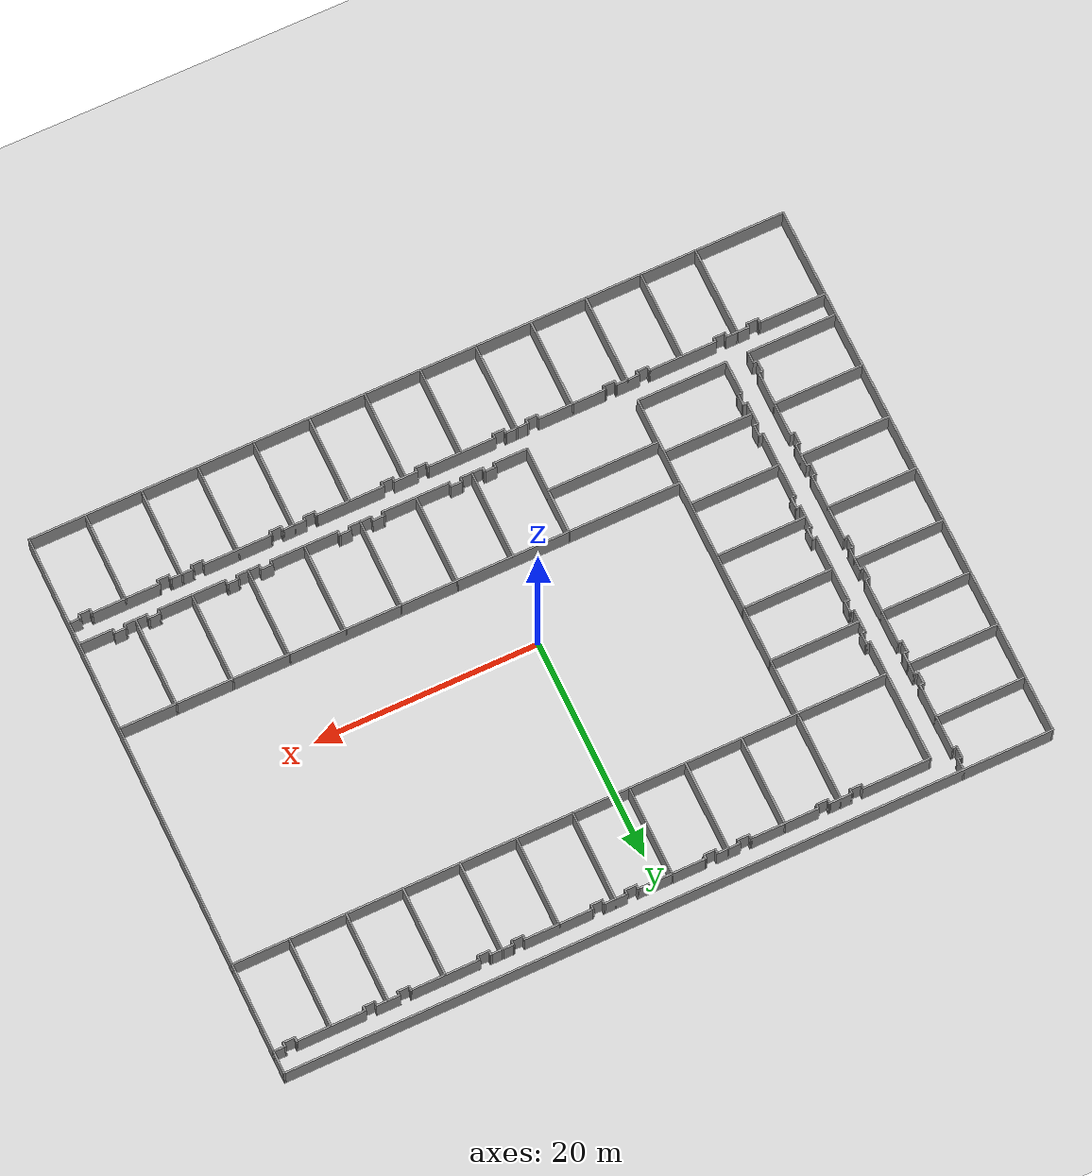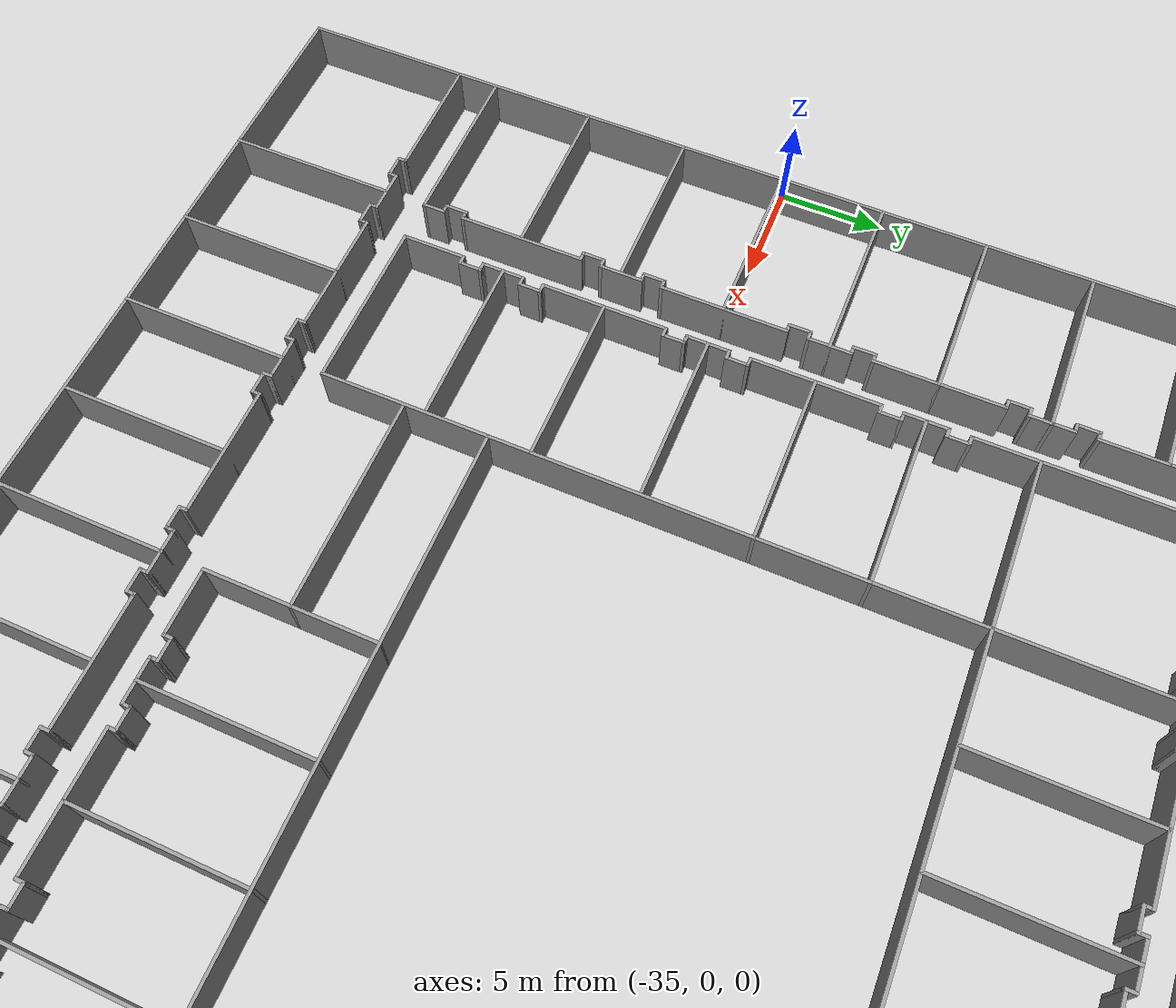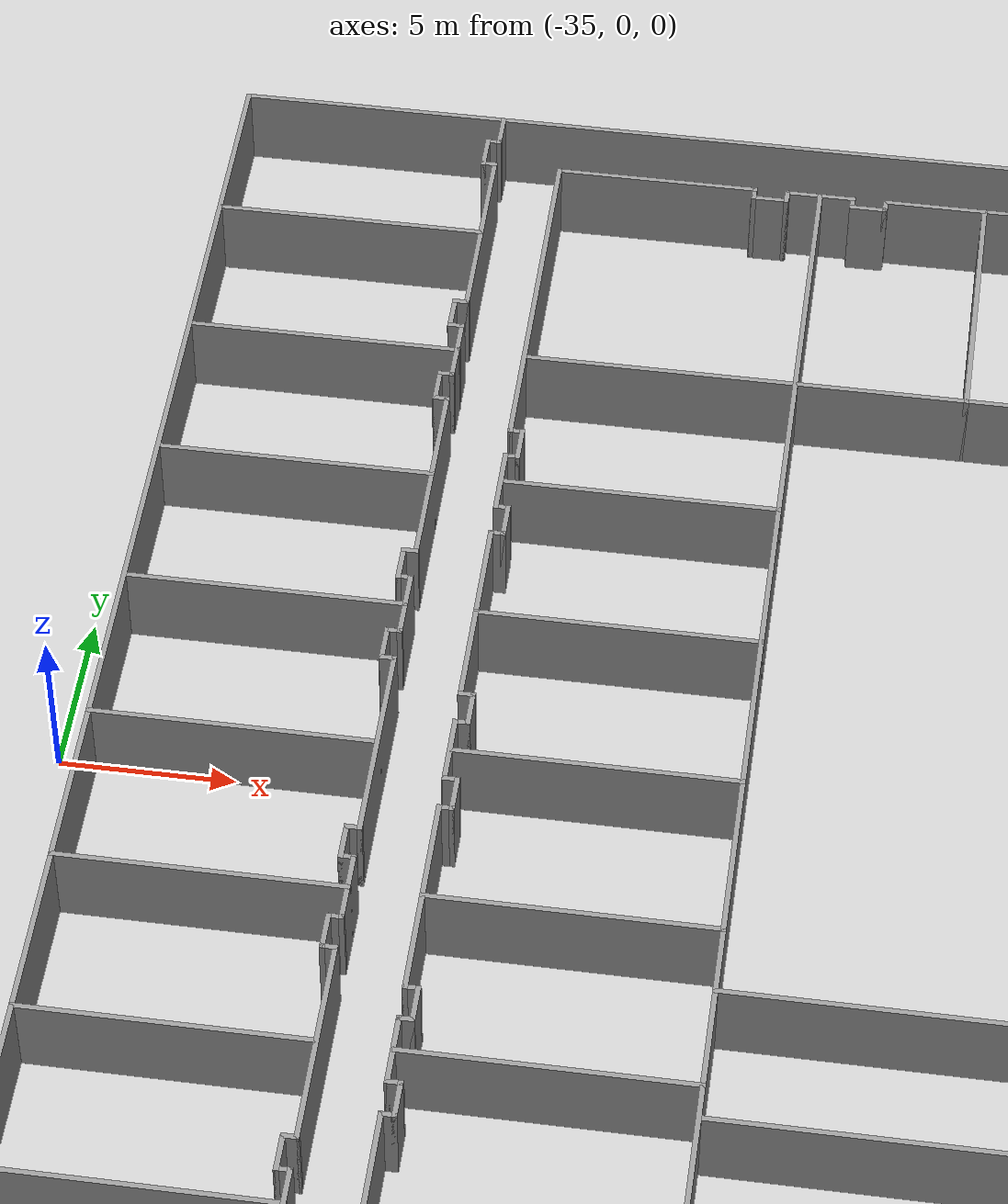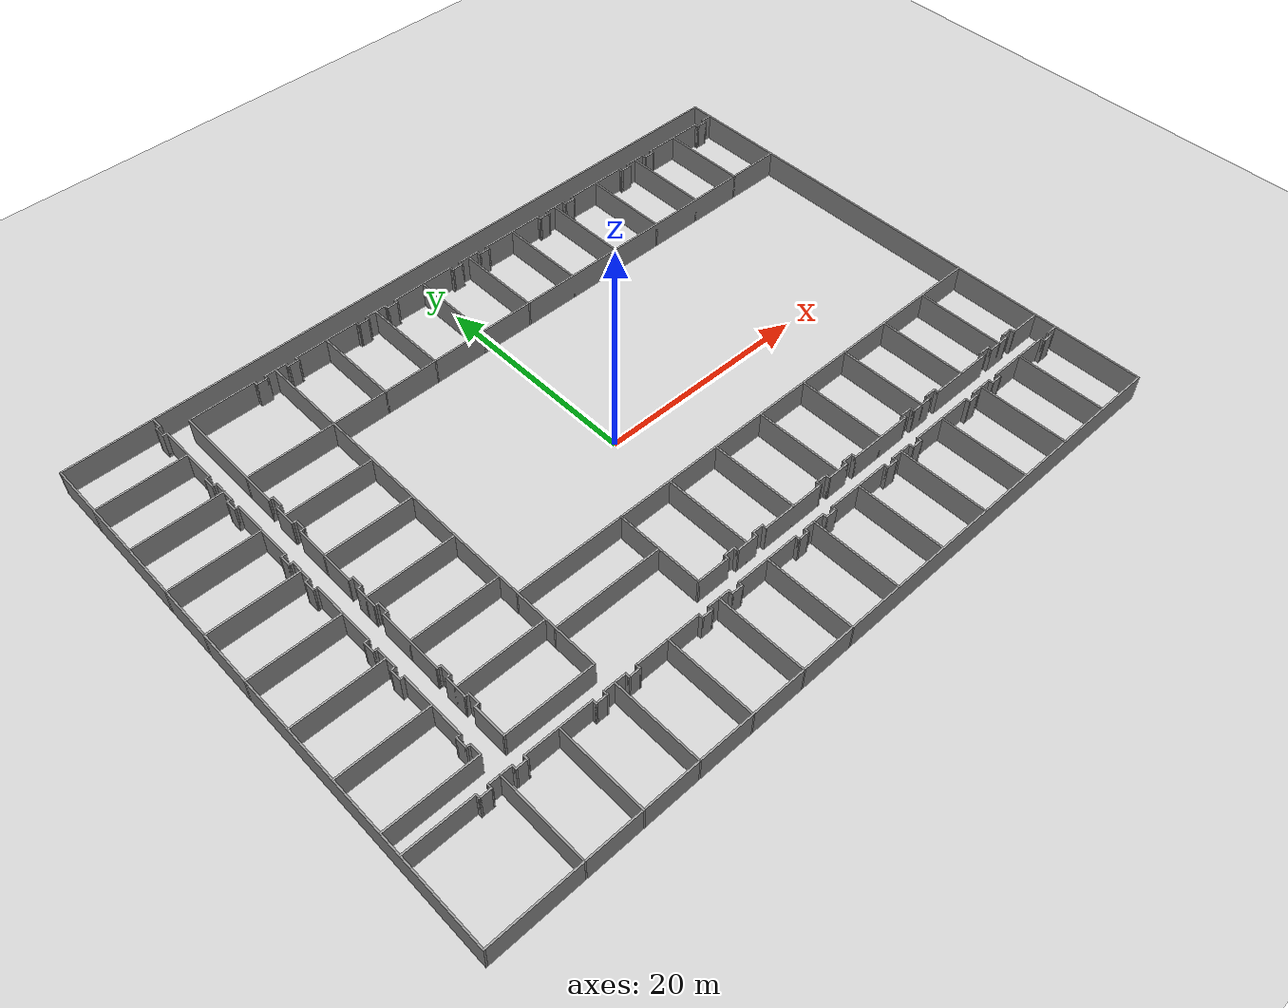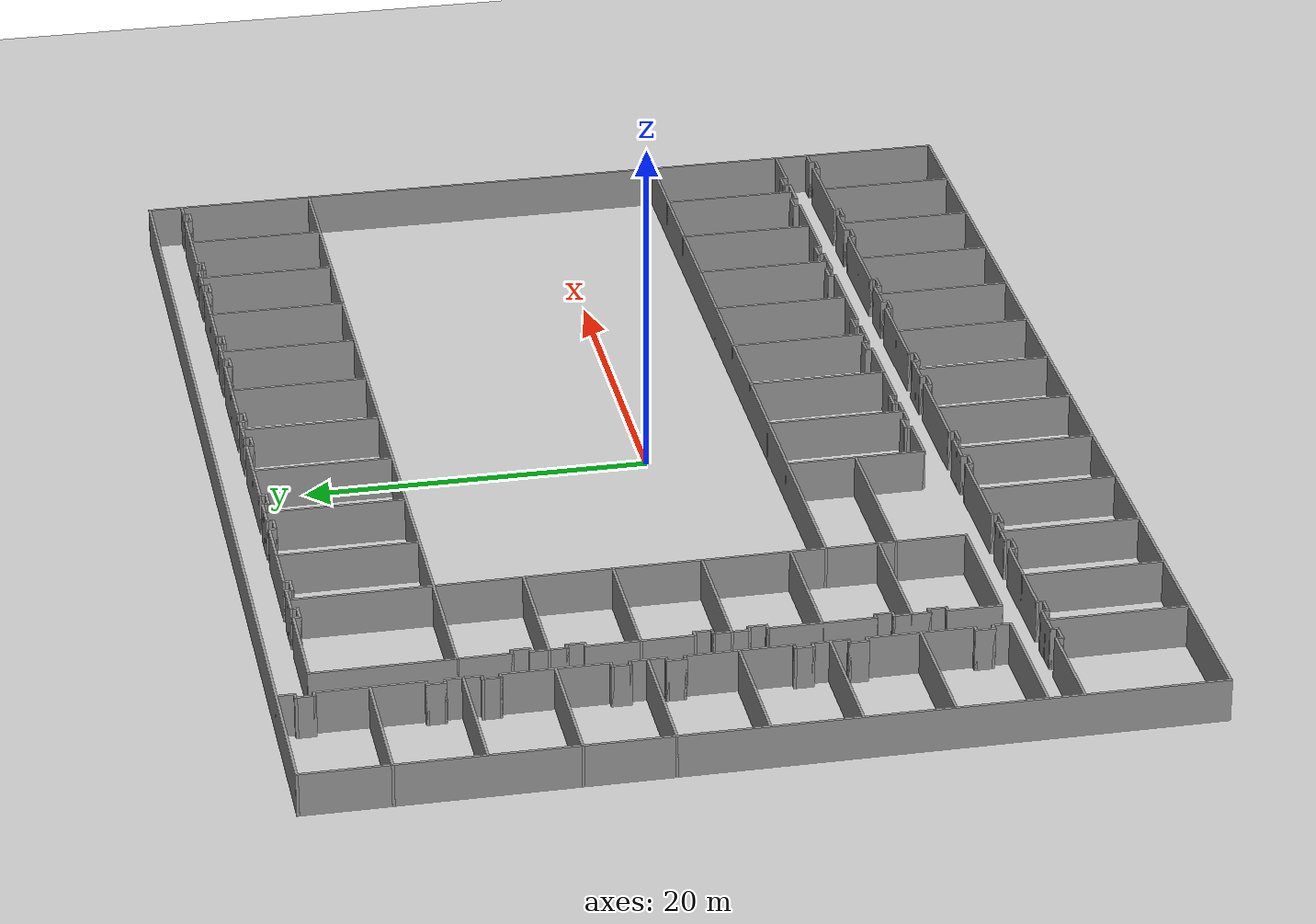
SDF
<sdf version="1.7">
 <world name="default">
  <light name="sun" type="directional">
   <pose>0 0 10 0 -0 0</pose>
   <diffuse>0.8 0.8 0.8 1</diffuse>
   <specular>0.2 0.2 0.2 1</specular>
   <attenuation>
    <range>1000</range>
    <constant>0.9</constant>
    <linear>0.01</linear>
    <quadratic>0.001</quadratic>
   </attenuation>
   <direction>-0.5 0.1 -0.9</direction>
   <spot><inner_angle>0</inner_angle><outer_angle>0</outer_angle><falloff>0</falloff></spot>
  </light>
  <model name="ground_plane">
   <static>1</static>
   <link name="link">
    <collision name="collision">
     <geometry><plane><normal>0 0 1</normal><size>100 100</size></plane></geometry>
     <surface>
      <contact><collide_bitmask>65535</collide_bitmask></contact>
      <friction><ode><mu>100</mu><mu2>50</mu2></ode></friction>
     </surface>
    </collision>
    <visual name="visual">
     <cast_shadows>0</cast_shadows>
     <geometry><plane><normal>0 0 1</normal><size>100 100</size></plane></geometry>
     <material>
      <script><uri>file://media/materials/scripts/gazebo.material</uri><name>Gazebo/Grey</name></script>
     </material>
    </visual>
   </link>
  </model>
  <gravity>0 0 -9.8</gravity>
  <magnetic_field>6e-06 2.3e-05 -4.2e-05</magnetic_field>
  <atmosphere type="adiabatic"/>
  <physics type="ode">
   <max_step_size>0.001</max_step_size>
   <real_time_factor>1</real_time_factor>
   <real_time_update_rate>1000</real_time_update_rate>
  </physics>
  <scene><ambient>0.4 0.4 0.4 1</ambient><background>0.7 0.7 0.7 1</background><shadows>1</shadows></scene>
  <audio><device>default</device></audio>
  <spherical_coordinates>
   <surface_model>EARTH_WGS84</surface_model>
   <latitude_deg>0</latitude_deg>
   <longitude_deg>0</longitude_deg>
   <elevation>0</elevation>
   <heading_deg>0</heading_deg>
  </spherical_coordinates>
  <model name="hallway">
   <link name="Wall_0">
    <collision name="Wall_0_Collision">
     <geometry><box><size>68.15 0.15 2.5</size></box></geometry>
     <pose>0 0 1.25 0 -0 0</pose>
    </collision>
    <visual name="Wall_0_Visual">
     <pose>0 0 1.25 0 -0 0</pose>
     <geometry><box><size>68.15 0.15 2.5</size></box></geometry>
     <material>
      <script><uri>file://media/materials/scripts/gazebo.material</uri><name>Gazebo/Grey</name></script>
      <ambient>1 1 1 1</ambient>
     </material>
     <meta><layer>0</layer></meta>
    </visual>
    <pose>0 25 0 0 -0 0</pose>
   </link>
   <link name="Wall_10">
    <collision name="Wall_10_Collision">
     <geometry><box><size>8.15 0.15 2.5</size></box></geometry>
     <pose>0 0 1.25 0 -0 0</pose>
    </collision>
    <visual name="Wall_10_Visual">
     <pose>0 0 1.25 0 -0 0</pose>
     <geometry><box><size>8.15 0.15 2.5</size></box></geometry>
     <material>
      <script><uri>file://media/materials/scripts/gazebo.material</uri><name>Gazebo/Grey</name></script>
      <ambient>1 1 1 1</ambient>
     </material>
     <meta><layer>0</layer></meta>
    </visual>
    <pose>-30 -15 0 0 -0 3.14159</pose>
   </link>
   <link name="Wall_100">
    <collision name="Wall_100_Collision">
     <geometry><box><size>8.15 0.15 2.5</size></box></geometry>
     <pose>0 0 1.25 0 -0 0</pose>
    </collision>
    <visual name="Wall_100_Visual">
     <pose>0 0 1.25 0 -0 0</pose>
     <geometry><box><size>8.15 0.15 2.5</size></box></geometry>
     <material>
      <script><uri>file://media/materials/scripts/gazebo.material</uri><name>Gazebo/Grey</name></script>
      <ambient>1 1 1 1</ambient>
     </material>
     <meta><layer>0</layer></meta>
    </visual>
    <pose>-30 -10 0 0 -0 3.14159</pose>
   </link>
   <link name="Wall_102">
    <collision name="Wall_102_Collision">
     <geometry><box><size>8.15 0.15 2.5</size></box></geometry>
     <pose>0 0 1.25 0 -0 0</pose>
    </collision>
    <visual name="Wall_102_Visual">
     <pose>0 0 1.25 0 -0 0</pose>
     <geometry><box><size>8.15 0.15 2.5</size></box></geometry>
     <material>
      <script><uri>file://media/materials/scripts/gazebo.material</uri><name>Gazebo/Grey</name></script>
      <ambient>1 1 1 1</ambient>
     </material>
     <meta><layer>0</layer></meta>
    </visual>
    <pose>-30 -5 0 0 -0 3.14159</pose>
   </link>
   <link name="Wall_104">
    <collision name="Wall_104_Collision">
     <geometry><box><size>8.15 0.15 2.5</size></box></geometry>
     <pose>0 0 1.25 0 -0 0</pose>
    </collision>
    <visual name="Wall_104_Visual">
     <pose>0 0 1.25 0 -0 0</pose>
     <geometry><box><size>8.15 0.15 2.5</size></box></geometry>
     <material>
      <script><uri>file://media/materials/scripts/gazebo.material</uri><name>Gazebo/Grey</name></script>
      <ambient>1 1 1 1</ambient>
     </material>
     <meta><layer>0</layer></meta>
    </visual>
    <pose>-30 0 0 0 -0 3.14159</pose>
   </link>
   <link name="Wall_106">
    <collision name="Wall_106_Collision">
     <geometry><box><size>8.15 0.15 2.5</size></box></geometry>
     <pose>0 0 1.25 0 -0 0</pose>
    </collision>
    <visual name="Wall_106_Visual">
     <pose>0 0 1.25 0 -0 0</pose>
     <geometry><box><size>8.15 0.15 2.5</size></box></geometry>
     <material>
      <script><uri>file://media/materials/scripts/gazebo.material</uri><name>Gazebo/Grey</name></script>
      <ambient>1 1 1 1</ambient>
     </material>
     <meta><layer>0</layer></meta>
    </visual>
    <pose>-30 5 0 0 -0 3.14159</pose>
   </link>
   <link name="Wall_108">
    <collision name="Wall_108_Collision">
     <geometry><box><size>8.15 0.15 2.5</size></box></geometry>
     <pose>0 0 1.25 0 -0 0</pose>
    </collision>
    <visual name="Wall_108_Visual">
     <pose>0 0 1.25 0 -0 0</pose>
     <geometry><box><size>8.15 0.15 2.5</size></box></geometry>
     <material>
      <script><uri>file://media/materials/scripts/gazebo.material</uri><name>Gazebo/Grey</name></script>
      <ambient>1 1 1 1</ambient>
     </material>
     <meta><layer>0</layer></meta>
    </visual>
    <pose>-30 10 0 0 -0 3.14159</pose>
   </link>
   <link name="Wall_110">
    <collision name="Wall_110_Collision">
     <geometry><box><size>8.15 0.15 2.5</size></box></geometry>
     <pose>0 0 1.25 0 -0 0</pose>
    </collision>
    <visual name="Wall_110_Visual">
     <pose>0 0 1.25 0 -0 0</pose>
     <geometry><box><size>8.15 0.15 2.5</size></box></geometry>
     <material>
      <script><uri>file://media/materials/scripts/gazebo.material</uri><name>Gazebo/Grey</name></script>
      <ambient>1 1 1 1</ambient>
     </material>
     <meta><layer>0</layer></meta>
    </visual>
    <pose>-29.9799 15 0 0 -0 3.14159</pose>
   </link>
   <link name="Wall_112">
    <collision name="Wall_112_Collision">
     <geometry><box><size>8.15 0.15 2.5</size></box></geometry>
     <pose>0 0 1.25 0 -0 0</pose>
    </collision>
    <visual name="Wall_112_Visual">
     <pose>0 0 1.25 0 -0 0</pose>
     <geometry><box><size>8.15 0.15 2.5</size></box></geometry>
     <material>
      <script><uri>file://media/materials/scripts/gazebo.material</uri><name>Gazebo/Grey</name></script>
      <ambient>1 1 1 1</ambient>
     </material>
     <meta><layer>0</layer></meta>
    </visual>
    <pose>-30 20 0 0 -0 3.14159</pose>
   </link>
   <link name="Wall_14">
    <collision name="Wall_14_Collision">
     <geometry><box><size>38.15 0.15 2.5</size></box></geometry>
     <pose>0 0 1.25 0 -0 0</pose>
    </collision>
    <visual name="Wall_14_Visual">
     <pose>0 0 1.25 0 -0 0</pose>
     <geometry><box><size>38.15 0.15 2.5</size></box></geometry>
     <material>
      <script><uri>file://media/materials/scripts/gazebo.material</uri><name>Gazebo/Grey</name></script>
      <ambient>1 1 1 1</ambient>
     </material>
     <meta><layer>0</layer></meta>
    </visual>
    <pose>-16 4 0 0 -0 1.5708</pose>
   </link>
   <link name="Wall_142">
    <collision name="Wall_142_Collision">
     <geometry><box><size>1.15 0.15 2.5</size></box></geometry>
     <pose>0 0 1.25 0 -0 0</pose>
    </collision>
    <visual name="Wall_142_Visual">
     <pose>0 0 1.25 0 -0 0</pose>
     <geometry><box><size>1.15 0.15 2.5</size></box></geometry>
     <material>
      <script><uri>file://media/materials/scripts/gazebo.material</uri><name>Gazebo/Grey</name></script>
      <ambient>1 1 1 1</ambient>
     </material>
     <meta><layer>0</layer></meta>
    </visual>
    <pose>-26 24.5 0 0 -0 -1.5708</pose>
   </link>
   <link name="Wall_144">
    <collision name="Wall_144_Collision">
     <geometry><box><size>0.5 0.15 2.5</size></box></geometry>
     <pose>0 0 1.25 0 -0 0</pose>
    </collision>
    <visual name="Wall_144_Visual">
     <pose>0 0 1.25 0 -0 0</pose>
     <geometry><box><size>0.5 0.15 2.5</size></box></geometry>
     <material>
      <script><uri>file://media/materials/scripts/gazebo.material</uri><name>Gazebo/Grey</name></script>
      <ambient>1 1 1 1</ambient>
     </material>
     <meta><layer>0</layer></meta>
    </visual>
    <pose>-26.175 24 0 0 -0 3.14159</pose>
   </link>
   <link name="Wall_145">
    <collision name="Wall_145_Collision">
     <geometry><box><size>1.15 0.15 2.5</size></box></geometry>
     <pose>0 0 1.25 0 -0 0</pose>
    </collision>
    <visual name="Wall_145_Visual">
     <pose>0 0 1.25 0 -0 0</pose>
     <geometry><box><size>1.15 0.15 2.5</size></box></geometry>
     <material>
      <script><uri>file://media/materials/scripts/gazebo.material</uri><name>Gazebo/Grey</name></script>
      <ambient>1 1 1 1</ambient>
     </material>
     <meta><layer>0</layer></meta>
    </visual>
    <pose>-26.35 23.5 0 0 -0 -1.5708</pose>
   </link>
   <link name="Wall_147">
    <collision name="Wall_147_Collision">
     <geometry><box><size>0.5 0.15 2.5</size></box></geometry>
     <pose>0 0 1.25 0 -0 0</pose>
    </collision>
    <visual name="Wall_147_Visual">
     <pose>0 0 1.25 0 -0 0</pose>
     <geometry><box><size>0.5 0.15 2.5</size></box></geometry>
     <material>
      <script><uri>file://media/materials/scripts/gazebo.material</uri><name>Gazebo/Grey</name></script>
      <ambient>1 1 1 1</ambient>
     </material>
     <meta><layer>0</layer></meta>
    </visual>
    <pose>-26.175 23 0 0 -0 0</pose>
   </link>
   <link name="Wall_148">
    <collision name="Wall_148_Collision">
     <geometry><box><size>6.15 0.15 2.5</size></box></geometry>
     <pose>0 0 1.25 0 -0 0</pose>
    </collision>
    <visual name="Wall_148_Visual">
     <pose>0 0 1.25 0 -0 0</pose>
     <geometry><box><size>6.15 0.15 2.5</size></box></geometry>
     <material>
      <script><uri>file://media/materials/scripts/gazebo.material</uri><name>Gazebo/Grey</name></script>
      <ambient>1 1 1 1</ambient>
     </material>
     <meta><layer>0</layer></meta>
    </visual>
    <pose>-26 20 0 0 -0 -1.5708</pose>
   </link>
   <link name="Wall_150">
    <collision name="Wall_150_Collision">
     <geometry><box><size>0.5 0.15 2.5</size></box></geometry>
     <pose>0 0 1.25 0 -0 0</pose>
    </collision>
    <visual name="Wall_150_Visual">
     <pose>0 0 1.25 0 -0 0</pose>
     <geometry><box><size>0.5 0.15 2.5</size></box></geometry>
     <material>
      <script><uri>file://media/materials/scripts/gazebo.material</uri><name>Gazebo/Grey</name></script>
      <ambient>1 1 1 1</ambient>
     </material>
     <meta><layer>0</layer></meta>
    </visual>
    <pose>-26.175 17 0 0 -0 3.14159</pose>
   </link>
   <link name="Wall_151">
    <collision name="Wall_151_Collision">
     <geometry><box><size>1.15 0.15 2.5</size></box></geometry>
     <pose>0 0 1.25 0 -0 0</pose>
    </collision>
    <visual name="Wall_151_Visual">
     <pose>0 0 1.25 0 -0 0</pose>
     <geometry><box><size>1.15 0.15 2.5</size></box></geometry>
     <material>
      <script><uri>file://media/materials/scripts/gazebo.material</uri><name>Gazebo/Grey</name></script>
      <ambient>1 1 1 1</ambient>
     </material>
     <meta><layer>0</layer></meta>
    </visual>
    <pose>-26.35 16.5 0 0 -0 -1.5708</pose>
   </link>
   <link name="Wall_153">
    <collision name="Wall_153_Collision">
     <geometry><box><size>0.5 0.15 2.5</size></box></geometry>
     <pose>0 0 1.25 0 -0 0</pose>
    </collision>
    <visual name="Wall_153_Visual">
     <pose>0 0 1.25 0 -0 0</pose>
     <geometry><box><size>0.5 0.15 2.5</size></box></geometry>
     <material>
      <script><uri>file://media/materials/scripts/gazebo.material</uri><name>Gazebo/Grey</name></script>
      <ambient>1 1 1 1</ambient>
     </material>
     <meta><layer>0</layer></meta>
    </visual>
    <pose>-26.175 16 0 0 -0 0</pose>
   </link>
   <link name="Wall_154">
    <collision name="Wall_154_Collision">
     <geometry><box><size>2.15 0.15 2.5</size></box></geometry>
     <pose>0 0 1.25 0 -0 0</pose>
    </collision>
    <visual name="Wall_154_Visual">
     <pose>0 0 1.25 0 -0 0</pose>
     <geometry><box><size>2.15 0.15 2.5</size></box></geometry>
     <material>
      <script><uri>file://media/materials/scripts/gazebo.material</uri><name>Gazebo/Grey</name></script>
      <ambient>1 1 1 1</ambient>
     </material>
     <meta><layer>0</layer></meta>
    </visual>
    <pose>-26 15 0 0 -0 -1.5708</pose>
   </link>
   <link name="Wall_159">
    <collision name="Wall_159_Collision">
     <geometry><box><size>0.5 0.15 2.5</size></box></geometry>
     <pose>0 0 1.25 0 -0 0</pose>
    </collision>
    <visual name="Wall_159_Visual">
     <pose>0 0 1.25 0 -0 0</pose>
     <geometry><box><size>0.5 0.15 2.5</size></box></geometry>
     <material>
      <script><uri>file://media/materials/scripts/gazebo.material</uri><name>Gazebo/Grey</name></script>
      <ambient>1 1 1 1</ambient>
     </material>
     <meta><layer>0</layer></meta>
    </visual>
    <pose>-26.175 14 0 0 -0 3.14159</pose>
   </link>
   <link name="Wall_16">
    <collision name="Wall_16_Collision">
     <geometry><box><size>8.15 0.15 2.5</size></box></geometry>
     <pose>0 0 1.25 0 -0 0</pose>
    </collision>
    <visual name="Wall_16_Visual">
     <pose>0 0 1.25 0 -0 0</pose>
     <geometry><box><size>8.15 0.15 2.5</size></box></geometry>
     <material>
      <script><uri>file://media/materials/scripts/gazebo.material</uri><name>Gazebo/Grey</name></script>
      <ambient>1 1 1 1</ambient>
     </material>
     <meta><layer>0</layer></meta>
    </visual>
    <pose>-20 -15 0 0 -0 3.14159</pose>
   </link>
   <link name="Wall_160">
    <collision name="Wall_160_Collision">
     <geometry><box><size>1.15 0.15 2.5</size></box></geometry>
     <pose>0 0 1.25 0 -0 0</pose>
    </collision>
    <visual name="Wall_160_Visual">
     <pose>0 0 1.25 0 -0 0</pose>
     <geometry><box><size>1.15 0.15 2.5</size></box></geometry>
     <material>
      <script><uri>file://media/materials/scripts/gazebo.material</uri><name>Gazebo/Grey</name></script>
      <ambient>1 1 1 1</ambient>
     </material>
     <meta><layer>0</layer></meta>
    </visual>
    <pose>-26.35 13.5 0 0 -0 -1.5708</pose>
   </link>
   <link name="Wall_162">
    <collision name="Wall_162_Collision">
     <geometry><box><size>0.5 0.15 2.5</size></box></geometry>
     <pose>0 0 1.25 0 -0 0</pose>
    </collision>
    <visual name="Wall_162_Visual">
     <pose>0 0 1.25 0 -0 0</pose>
     <geometry><box><size>0.5 0.15 2.5</size></box></geometry>
     <material>
      <script><uri>file://media/materials/scripts/gazebo.material</uri><name>Gazebo/Grey</name></script>
      <ambient>1 1 1 1</ambient>
     </material>
     <meta><layer>0</layer></meta>
    </visual>
    <pose>-26.175 13 0 0 -0 0</pose>
   </link>
   <link name="Wall_163">
    <collision name="Wall_163_Collision">
     <geometry><box><size>6.15 0.15 2.5</size></box></geometry>
     <pose>0 0 1.25 0 -0 0</pose>
    </collision>
    <visual name="Wall_163_Visual">
     <pose>0 0 1.25 0 -0 0</pose>
     <geometry><box><size>6.15 0.15 2.5</size></box></geometry>
     <material>
      <script><uri>file://media/materials/scripts/gazebo.material</uri><name>Gazebo/Grey</name></script>
      <ambient>1 1 1 1</ambient>
     </material>
     <meta><layer>0</layer></meta>
    </visual>
    <pose>-26 10 0 0 -0 -1.5708</pose>
   </link>
   <link name="Wall_165">
    <collision name="Wall_165_Collision">
     <geometry><box><size>0.5 0.15 2.5</size></box></geometry>
     <pose>0 0 1.25 0 -0 0</pose>
    </collision>
    <visual name="Wall_165_Visual">
     <pose>0 0 1.25 0 -0 0</pose>
     <geometry><box><size>0.5 0.15 2.5</size></box></geometry>
     <material>
      <script><uri>file://media/materials/scripts/gazebo.material</uri><name>Gazebo/Grey</name></script>
      <ambient>1 1 1 1</ambient>
     </material>
     <meta><layer>0</layer></meta>
    </visual>
    <pose>-26.175 7 0 0 -0 3.14159</pose>
   </link>
   <link name="Wall_166">
    <collision name="Wall_166_Collision">
     <geometry><box><size>1.15 0.15 2.5</size></box></geometry>
     <pose>0 0 1.25 0 -0 0</pose>
    </collision>
    <visual name="Wall_166_Visual">
     <pose>0 0 1.25 0 -0 0</pose>
     <geometry><box><size>1.15 0.15 2.5</size></box></geometry>
     <material>
      <script><uri>file://media/materials/scripts/gazebo.material</uri><name>Gazebo/Grey</name></script>
      <ambient>1 1 1 1</ambient>
     </material>
     <meta><layer>0</layer></meta>
    </visual>
    <pose>-26.35 6.5 0 0 -0 -1.5708</pose>
   </link>
   <link name="Wall_168">
    <collision name="Wall_168_Collision">
     <geometry><box><size>0.5 0.15 2.5</size></box></geometry>
     <pose>0 0 1.25 0 -0 0</pose>
    </collision>
    <visual name="Wall_168_Visual">
     <pose>0 0 1.25 0 -0 0</pose>
     <geometry><box><size>0.5 0.15 2.5</size></box></geometry>
     <material>
      <script><uri>file://media/materials/scripts/gazebo.material</uri><name>Gazebo/Grey</name></script>
      <ambient>1 1 1 1</ambient>
     </material>
     <meta><layer>0</layer></meta>
    </visual>
    <pose>-26.175 6 0 0 -0 0</pose>
   </link>
   <link name="Wall_169">
    <collision name="Wall_169_Collision">
     <geometry><box><size>2.15 0.15 2.5</size></box></geometry>
     <pose>0 0 1.25 0 -0 0</pose>
    </collision>
    <visual name="Wall_169_Visual">
     <pose>0 0 1.25 0 -0 0</pose>
     <geometry><box><size>2.15 0.15 2.5</size></box></geometry>
     <material>
      <script><uri>file://media/materials/scripts/gazebo.material</uri><name>Gazebo/Grey</name></script>
      <ambient>1 1 1 1</ambient>
     </material>
     <meta><layer>0</layer></meta>
    </visual>
    <pose>-26 5 0 0 -0 -1.5708</pose>
   </link>
   <link name="Wall_174">
    <collision name="Wall_174_Collision">
     <geometry><box><size>0.5 0.15 2.5</size></box></geometry>
     <pose>0 0 1.25 0 -0 0</pose>
    </collision>
    <visual name="Wall_174_Visual">
     <pose>0 0 1.25 0 -0 0</pose>
     <geometry><box><size>0.5 0.15 2.5</size></box></geometry>
     <material>
      <script><uri>file://media/materials/scripts/gazebo.material</uri><name>Gazebo/Grey</name></script>
      <ambient>1 1 1 1</ambient>
     </material>
     <meta><layer>0</layer></meta>
    </visual>
    <pose>-26.175 4 0 0 -0 3.14159</pose>
   </link>
   <link name="Wall_175">
    <collision name="Wall_175_Collision">
     <geometry><box><size>1.15 0.15 2.5</size></box></geometry>
     <pose>0 0 1.25 0 -0 0</pose>
    </collision>
    <visual name="Wall_175_Visual">
     <pose>0 0 1.25 0 -0 0</pose>
     <geometry><box><size>1.15 0.15 2.5</size></box></geometry>
     <material>
      <script><uri>file://media/materials/scripts/gazebo.material</uri><name>Gazebo/Grey</name></script>
      <ambient>1 1 1 1</ambient>
     </material>
     <meta><layer>0</layer></meta>
    </visual>
    <pose>-26.35 3.5 0 0 -0 -1.5708</pose>
   </link>
   <link name="Wall_177">
    <collision name="Wall_177_Collision">
     <geometry><box><size>0.5 0.15 2.5</size></box></geometry>
     <pose>0 0 1.25 0 -0 0</pose>
    </collision>
    <visual name="Wall_177_Visual">
     <pose>0 0 1.25 0 -0 0</pose>
     <geometry><box><size>0.5 0.15 2.5</size></box></geometry>
     <material>
      <script><uri>file://media/materials/scripts/gazebo.material</uri><name>Gazebo/Grey</name></script>
      <ambient>1 1 1 1</ambient>
     </material>
     <meta><layer>0</layer></meta>
    </visual>
    <pose>-26.175 3 0 0 -0 0</pose>
   </link>
   <link name="Wall_178">
    <collision name="Wall_178_Collision">
     <geometry><box><size>6.15 0.15 2.5</size></box></geometry>
     <pose>0 0 1.25 0 -0 0</pose>
    </collision>
    <visual name="Wall_178_Visual">
     <pose>0 0 1.25 0 -0 0</pose>
     <geometry><box><size>6.15 0.15 2.5</size></box></geometry>
     <material>
      <script><uri>file://media/materials/scripts/gazebo.material</uri><name>Gazebo/Grey</name></script>
      <ambient>1 1 1 1</ambient>
     </material>
     <meta><layer>0</layer></meta>
    </visual>
    <pose>-26 0 0 0 -0 -1.5708</pose>
   </link>
   <link name="Wall_180">
    <collision name="Wall_180_Collision">
     <geometry><box><size>0.5 0.15 2.5</size></box></geometry>
     <pose>0 0 1.25 0 -0 0</pose>
    </collision>
    <visual name="Wall_180_Visual">
     <pose>0 0 1.25 0 -0 0</pose>
     <geometry><box><size>0.5 0.15 2.5</size></box></geometry>
     <material>
      <script><uri>file://media/materials/scripts/gazebo.material</uri><name>Gazebo/Grey</name></script>
      <ambient>1 1 1 1</ambient>
     </material>
     <meta><layer>0</layer></meta>
    </visual>
    <pose>-26.175 -3 0 0 -0 3.14159</pose>
   </link>
   <link name="Wall_181">
    <collision name="Wall_181_Collision">
     <geometry><box><size>1.15 0.15 2.5</size></box></geometry>
     <pose>0 0 1.25 0 -0 0</pose>
    </collision>
    <visual name="Wall_181_Visual">
     <pose>0 0 1.25 0 -0 0</pose>
     <geometry><box><size>1.15 0.15 2.5</size></box></geometry>
     <material>
      <script><uri>file://media/materials/scripts/gazebo.material</uri><name>Gazebo/Grey</name></script>
      <ambient>1 1 1 1</ambient>
     </material>
     <meta><layer>0</layer></meta>
    </visual>
    <pose>-26.35 -3.5 0 0 -0 -1.5708</pose>
   </link>
   <link name="Wall_183">
    <collision name="Wall_183_Collision">
     <geometry><box><size>0.5 0.15 2.5</size></box></geometry>
     <pose>0 0 1.25 0 -0 0</pose>
    </collision>
    <visual name="Wall_183_Visual">
     <pose>0 0 1.25 0 -0 0</pose>
     <geometry><box><size>0.5 0.15 2.5</size></box></geometry>
     <material>
      <script><uri>file://media/materials/scripts/gazebo.material</uri><name>Gazebo/Grey</name></script>
      <ambient>1 1 1 1</ambient>
     </material>
     <meta><layer>0</layer></meta>
    </visual>
    <pose>-26.175 -4 0 0 -0 0</pose>
   </link>
   <link name="Wall_184">
    <collision name="Wall_184_Collision">
     <geometry><box><size>2.15 0.15 2.5</size></box></geometry>
     <pose>0 0 1.25 0 -0 0</pose>
    </collision>
    <visual name="Wall_184_Visual">
     <pose>0 0 1.25 0 -0 0</pose>
     <geometry><box><size>2.15 0.15 2.5</size></box></geometry>
     <material>
      <script><uri>file://media/materials/scripts/gazebo.material</uri><name>Gazebo/Grey</name></script>
      <ambient>1 1 1 1</ambient>
     </material>
     <meta><layer>0</layer></meta>
    </visual>
    <pose>-26 -5 0 0 -0 -1.5708</pose>
   </link>
   <link name="Wall_186">
    <collision name="Wall_186_Collision">
     <geometry><box><size>0.5 0.15 2.5</size></box></geometry>
     <pose>0 0 1.25 0 -0 0</pose>
    </collision>
    <visual name="Wall_186_Visual">
     <pose>0 0 1.25 0 -0 0</pose>
     <geometry><box><size>0.5 0.15 2.5</size></box></geometry>
     <material>
      <script><uri>file://media/materials/scripts/gazebo.material</uri><name>Gazebo/Grey</name></script>
      <ambient>1 1 1 1</ambient>
     </material>
     <meta><layer>0</layer></meta>
    </visual>
    <pose>-26.175 -6 0 0 -0 3.14159</pose>
   </link>
   <link name="Wall_187">
    <collision name="Wall_187_Collision">
     <geometry><box><size>1.15 0.15 2.5</size></box></geometry>
     <pose>0 0 1.25 0 -0 0</pose>
    </collision>
    <visual name="Wall_187_Visual">
     <pose>0 0 1.25 0 -0 0</pose>
     <geometry><box><size>1.15 0.15 2.5</size></box></geometry>
     <material>
      <script><uri>file://media/materials/scripts/gazebo.material</uri><name>Gazebo/Grey</name></script>
      <ambient>1 1 1 1</ambient>
     </material>
     <meta><layer>0</layer></meta>
    </visual>
    <pose>-26.35 -6.5 0 0 -0 -1.5708</pose>
   </link>
   <link name="Wall_189">
    <collision name="Wall_189_Collision">
     <geometry><box><size>0.5 0.15 2.5</size></box></geometry>
     <pose>0 0 1.25 0 -0 0</pose>
    </collision>
    <visual name="Wall_189_Visual">
     <pose>0 0 1.25 0 -0 0</pose>
     <geometry><box><size>0.5 0.15 2.5</size></box></geometry>
     <material>
      <script><uri>file://media/materials/scripts/gazebo.material</uri><name>Gazebo/Grey</name></script>
      <ambient>1 1 1 1</ambient>
     </material>
     <meta><layer>0</layer></meta>
    </visual>
    <pose>-26.175 -7 0 0 -0 0</pose>
   </link>
   <link name="Wall_190">
    <collision name="Wall_190_Collision">
     <geometry><box><size>6.15 0.15 2.5</size></box></geometry>
     <pose>0 0 1.25 0 -0 0</pose>
    </collision>
    <visual name="Wall_190_Visual">
     <pose>0 0 1.25 0 -0 0</pose>
     <geometry><box><size>6.15 0.15 2.5</size></box></geometry>
     <material>
      <script><uri>file://media/materials/scripts/gazebo.material</uri><name>Gazebo/Grey</name></script>
      <ambient>1 1 1 1</ambient>
     </material>
     <meta><layer>0</layer></meta>
    </visual>
    <pose>-26 -10 0 0 -0 -1.5708</pose>
   </link>
   <link name="Wall_192">
    <collision name="Wall_192_Collision">
     <geometry><box><size>0.5 0.15 2.5</size></box></geometry>
     <pose>0 0 1.25 0 -0 0</pose>
    </collision>
    <visual name="Wall_192_Visual">
     <pose>0 0 1.25 0 -0 0</pose>
     <geometry><box><size>0.5 0.15 2.5</size></box></geometry>
     <material>
      <script><uri>file://media/materials/scripts/gazebo.material</uri><name>Gazebo/Grey</name></script>
      <ambient>1 1 1 1</ambient>
     </material>
     <meta><layer>0</layer></meta>
    </visual>
    <pose>-26.175 -13 0 0 -0 3.14159</pose>
   </link>
   <link name="Wall_193">
    <collision name="Wall_193_Collision">
     <geometry><box><size>1.15 0.15 2.5</size></box></geometry>
     <pose>0 0 1.25 0 -0 0</pose>
    </collision>
    <visual name="Wall_193_Visual">
     <pose>0 0 1.25 0 -0 0</pose>
     <geometry><box><size>1.15 0.15 2.5</size></box></geometry>
     <material>
      <script><uri>file://media/materials/scripts/gazebo.material</uri><name>Gazebo/Grey</name></script>
      <ambient>1 1 1 1</ambient>
     </material>
     <meta><layer>0</layer></meta>
    </visual>
    <pose>-26.35 -13.5 0 0 -0 -1.5708</pose>
   </link>
   <link name="Wall_195">
    <collision name="Wall_195_Collision">
     <geometry><box><size>0.5 0.15 2.5</size></box></geometry>
     <pose>0 0 1.25 0 -0 0</pose>
    </collision>
    <visual name="Wall_195_Visual">
     <pose>0 0 1.25 0 -0 0</pose>
     <geometry><box><size>0.5 0.15 2.5</size></box></geometry>
     <material>
      <script><uri>file://media/materials/scripts/gazebo.material</uri><name>Gazebo/Grey</name></script>
      <ambient>1 1 1 1</ambient>
     </material>
     <meta><layer>0</layer></meta>
    </visual>
    <pose>-26.175 -14 0 0 -0 0</pose>
   </link>
   <link name="Wall_196">
    <collision name="Wall_196_Collision">
     <geometry><box><size>1.15 0.15 2.5</size></box></geometry>
     <pose>0 0 1.25 0 -0 0</pose>
    </collision>
    <visual name="Wall_196_Visual">
     <pose>0 0 1.25 0 -0 0</pose>
     <geometry><box><size>1.15 0.15 2.5</size></box></geometry>
     <material>
      <script><uri>file://media/materials/scripts/gazebo.material</uri><name>Gazebo/Grey</name></script>
      <ambient>1 1 1 1</ambient>
     </material>
     <meta><layer>0</layer></meta>
    </visual>
    <pose>-26 -14.5 0 0 -0 -1.5708</pose>
   </link>
   <link name="Wall_198">
    <collision name="Wall_198_Collision">
     <geometry><box><size>6.15 0.15 2.5</size></box></geometry>
     <pose>0 0 1.25 0 -0 0</pose>
    </collision>
    <visual name="Wall_198_Visual">
     <pose>0 0 1.25 0 -0 0</pose>
     <geometry><box><size>6.15 0.15 2.5</size></box></geometry>
     <material>
      <script><uri>file://media/materials/scripts/gazebo.material</uri><name>Gazebo/Grey</name></script>
      <ambient>1 1 1 1</ambient>
     </material>
     <meta><layer>0</layer></meta>
    </visual>
    <pose>-31 -17 0 0 -0 0</pose>
   </link>
   <link name="Wall_2">
    <collision name="Wall_2_Collision">
     <geometry><box><size>50.15 0.15 2.5</size></box></geometry>
     <pose>0 0 1.25 0 -0 0</pose>
    </collision>
    <visual name="Wall_2_Visual">
     <pose>0 0 1.25 0 -0 0</pose>
     <geometry><box><size>50.15 0.15 2.5</size></box></geometry>
     <material>
      <script><uri>file://media/materials/scripts/gazebo.material</uri><name>Gazebo/Grey</name></script>
      <ambient>1 1 1 1</ambient>
     </material>
     <meta><layer>0</layer></meta>
    </visual>
    <pose>-34 0 0 0 -0 -1.5708</pose>
   </link>
   <link name="Wall_200">
    <collision name="Wall_200_Collision">
     <geometry><box><size>0.5 0.15 2.5</size></box></geometry>
     <pose>0 0 1.25 0 -0 0</pose>
    </collision>
    <visual name="Wall_200_Visual">
     <pose>0 0 1.25 0 -0 0</pose>
     <geometry><box><size>0.5 0.15 2.5</size></box></geometry>
     <material>
      <script><uri>file://media/materials/scripts/gazebo.material</uri><name>Gazebo/Grey</name></script>
      <ambient>1 1 1 1</ambient>
     </material>
     <meta><layer>0</layer></meta>
    </visual>
    <pose>-28 -17.175 0 0 -0 -1.5708</pose>
   </link>
   <link name="Wall_201">
    <collision name="Wall_201_Collision">
     <geometry><box><size>1.15 0.15 2.5</size></box></geometry>
     <pose>0 0 1.25 0 -0 0</pose>
    </collision>
    <visual name="Wall_201_Visual">
     <pose>0 0 1.25 0 -0 0</pose>
     <geometry><box><size>1.15 0.15 2.5</size></box></geometry>
     <material>
      <script><uri>file://media/materials/scripts/gazebo.material</uri><name>Gazebo/Grey</name></script>
      <ambient>1 1 1 1</ambient>
     </material>
     <meta><layer>0</layer></meta>
    </visual>
    <pose>-27.5 -17.35 0 0 -0 0</pose>
   </link>
   <link name="Wall_203">
    <collision name="Wall_203_Collision">
     <geometry><box><size>0.5 0.15 2.5</size></box></geometry>
     <pose>0 0 1.25 0 -0 0</pose>
    </collision>
    <visual name="Wall_203_Visual">
     <pose>0 0 1.25 0 -0 0</pose>
     <geometry><box><size>0.5 0.15 2.5</size></box></geometry>
     <material>
      <script><uri>file://media/materials/scripts/gazebo.material</uri><name>Gazebo/Grey</name></script>
      <ambient>1 1 1 1</ambient>
     </material>
     <meta><layer>0</layer></meta>
    </visual>
    <pose>-27 -17.175 0 0 -0 1.5708</pose>
   </link>
   <link name="Wall_204">
    <collision name="Wall_204_Collision">
     <geometry><box><size>2.15 0.15 2.5</size></box></geometry>
     <pose>0 0 1.25 0 -0 0</pose>
    </collision>
    <visual name="Wall_204_Visual">
     <pose>0 0 1.25 0 -0 0</pose>
     <geometry><box><size>2.15 0.15 2.5</size></box></geometry>
     <material>
      <script><uri>file://media/materials/scripts/gazebo.material</uri><name>Gazebo/Grey</name></script>
      <ambient>1 1 1 1</ambient>
     </material>
     <meta><layer>0</layer></meta>
    </visual>
    <pose>-26 -17 0 0 -0 0</pose>
   </link>
   <link name="Wall_206">
    <collision name="Wall_206_Collision">
     <geometry><box><size>0.5 0.15 2.5</size></box></geometry>
     <pose>0 0 1.25 0 -0 0</pose>
    </collision>
    <visual name="Wall_206_Visual">
     <pose>0 0 1.25 0 -0 0</pose>
     <geometry><box><size>0.5 0.15 2.5</size></box></geometry>
     <material>
      <script><uri>file://media/materials/scripts/gazebo.material</uri><name>Gazebo/Grey</name></script>
      <ambient>1 1 1 1</ambient>
     </material>
     <meta><layer>0</layer></meta>
    </visual>
    <pose>-25 -17.175 0 0 -0 -1.5708</pose>
   </link>
   <link name="Wall_207">
    <collision name="Wall_207_Collision">
     <geometry><box><size>1.15 0.15 2.5</size></box></geometry>
     <pose>0 0 1.25 0 -0 0</pose>
    </collision>
    <visual name="Wall_207_Visual">
     <pose>0 0 1.25 0 -0 0</pose>
     <geometry><box><size>1.15 0.15 2.5</size></box></geometry>
     <material>
      <script><uri>file://media/materials/scripts/gazebo.material</uri><name>Gazebo/Grey</name></script>
      <ambient>1 1 1 1</ambient>
     </material>
     <meta><layer>0</layer></meta>
    </visual>
    <pose>-24.5 -17.35 0 0 -0 0</pose>
   </link>
   <link name="Wall_209">
    <collision name="Wall_209_Collision">
     <geometry><box><size>0.5 0.15 2.5</size></box></geometry>
     <pose>0 0 1.25 0 -0 0</pose>
    </collision>
    <visual name="Wall_209_Visual">
     <pose>0 0 1.25 0 -0 0</pose>
     <geometry><box><size>0.5 0.15 2.5</size></box></geometry>
     <material>
      <script><uri>file://media/materials/scripts/gazebo.material</uri><name>Gazebo/Grey</name></script>
      <ambient>1 1 1 1</ambient>
     </material>
     <meta><layer>0</layer></meta>
    </visual>
    <pose>-24 -17.175 0 0 -0 1.5708</pose>
   </link>
   <link name="Wall_210">
    <collision name="Wall_210_Collision">
     <geometry><box><size>6.15 0.15 2.5</size></box></geometry>
     <pose>0 0 1.25 0 -0 0</pose>
    </collision>
    <visual name="Wall_210_Visual">
     <pose>0 0 1.25 0 -0 0</pose>
     <geometry><box><size>6.15 0.15 2.5</size></box></geometry>
     <material>
      <script><uri>file://media/materials/scripts/gazebo.material</uri><name>Gazebo/Grey</name></script>
      <ambient>1 1 1 1</ambient>
     </material>
     <meta><layer>0</layer></meta>
    </visual>
    <pose>-21 -17 0 0 -0 0</pose>
   </link>
   <link name="Wall_212">
    <collision name="Wall_212_Collision">
     <geometry><box><size>0.5 0.15 2.5</size></box></geometry>
     <pose>0 0 1.25 0 -0 0</pose>
    </collision>
    <visual name="Wall_212_Visual">
     <pose>0 0 1.25 0 -0 0</pose>
     <geometry><box><size>0.5 0.15 2.5</size></box></geometry>
     <material>
      <script><uri>file://media/materials/scripts/gazebo.material</uri><name>Gazebo/Grey</name></script>
      <ambient>1 1 1 1</ambient>
     </material>
     <meta><layer>0</layer></meta>
    </visual>
    <pose>-18 -17.175 0 0 -0 -1.5708</pose>
   </link>
   <link name="Wall_213">
    <collision name="Wall_213_Collision">
     <geometry><box><size>1.15 0.15 2.5</size></box></geometry>
     <pose>0 0 1.25 0 -0 0</pose>
    </collision>
    <visual name="Wall_213_Visual">
     <pose>0 0 1.25 0 -0 0</pose>
     <geometry><box><size>1.15 0.15 2.5</size></box></geometry>
     <material>
      <script><uri>file://media/materials/scripts/gazebo.material</uri><name>Gazebo/Grey</name></script>
      <ambient>1 1 1 1</ambient>
     </material>
     <meta><layer>0</layer></meta>
    </visual>
    <pose>-17.5 -17.35 0 0 -0 0</pose>
   </link>
   <link name="Wall_215">
    <collision name="Wall_215_Collision">
     <geometry><box><size>0.5 0.15 2.5</size></box></geometry>
     <pose>0 0 1.25 0 -0 0</pose>
    </collision>
    <visual name="Wall_215_Visual">
     <pose>0 0 1.25 0 -0 0</pose>
     <geometry><box><size>0.5 0.15 2.5</size></box></geometry>
     <material>
      <script><uri>file://media/materials/scripts/gazebo.material</uri><name>Gazebo/Grey</name></script>
      <ambient>1 1 1 1</ambient>
     </material>
     <meta><layer>0</layer></meta>
    </visual>
    <pose>-17 -17.175 0 0 -0 1.5708</pose>
   </link>
   <link name="Wall_216">
    <collision name="Wall_216_Collision">
     <geometry><box><size>2.15 0.15 2.5</size></box></geometry>
     <pose>0 0 1.25 0 -0 0</pose>
    </collision>
    <visual name="Wall_216_Visual">
     <pose>0 0 1.25 0 -0 0</pose>
     <geometry><box><size>2.15 0.15 2.5</size></box></geometry>
     <material>
      <script><uri>file://media/materials/scripts/gazebo.material</uri><name>Gazebo/Grey</name></script>
      <ambient>1 1 1 1</ambient>
     </material>
     <meta><layer>0</layer></meta>
    </visual>
    <pose>-16 -17 0 0 -0 0</pose>
   </link>
   <link name="Wall_218">
    <collision name="Wall_218_Collision">
     <geometry><box><size>0.5 0.15 2.5</size></box></geometry>
     <pose>0 0 1.25 0 -0 0</pose>
    </collision>
    <visual name="Wall_218_Visual">
     <pose>0 0 1.25 0 -0 0</pose>
     <geometry><box><size>0.5 0.15 2.5</size></box></geometry>
     <material>
      <script><uri>file://media/materials/scripts/gazebo.material</uri><name>Gazebo/Grey</name></script>
      <ambient>1 1 1 1</ambient>
     </material>
     <meta><layer>0</layer></meta>
    </visual>
    <pose>-15 -17.175 0 0 -0 -1.5708</pose>
   </link>
   <link name="Wall_219">
    <collision name="Wall_219_Collision">
     <geometry><box><size>1.15 0.15 2.5</size></box></geometry>
     <pose>0 0 1.25 0 -0 0</pose>
    </collision>
    <visual name="Wall_219_Visual">
     <pose>0 0 1.25 0 -0 0</pose>
     <geometry><box><size>1.15 0.15 2.5</size></box></geometry>
     <material>
      <script><uri>file://media/materials/scripts/gazebo.material</uri><name>Gazebo/Grey</name></script>
      <ambient>1 1 1 1</ambient>
     </material>
     <meta><layer>0</layer></meta>
    </visual>
    <pose>-14.5 -17.35 0 0 -0 0</pose>
   </link>
   <link name="Wall_22">
    <collision name="Wall_22_Collision">
     <geometry><box><size>10.15 0.15 2.5</size></box></geometry>
     <pose>0 0 1.25 0 -0 0</pose>
    </collision>
    <visual name="Wall_22_Visual">
     <pose>0 0 1.25 0 -0 0</pose>
     <geometry><box><size>10.15 0.15 2.5</size></box></geometry>
     <material>
      <script><uri>file://media/materials/scripts/gazebo.material</uri><name>Gazebo/Grey</name></script>
      <ambient>1 1 1 1</ambient>
     </material>
     <meta><layer>0</layer></meta>
    </visual>
    <pose>-11 -11 0 0 -0 0</pose>
   </link>
   <link name="Wall_221">
    <collision name="Wall_221_Collision">
     <geometry><box><size>0.5 0.15 2.5</size></box></geometry>
     <pose>0 0 1.25 0 -0 0</pose>
    </collision>
    <visual name="Wall_221_Visual">
     <pose>0 0 1.25 0 -0 0</pose>
     <geometry><box><size>0.5 0.15 2.5</size></box></geometry>
     <material>
      <script><uri>file://media/materials/scripts/gazebo.material</uri><name>Gazebo/Grey</name></script>
      <ambient>1 1 1 1</ambient>
     </material>
     <meta><layer>0</layer></meta>
    </visual>
    <pose>-14 -17.175 0 0 -0 1.5708</pose>
   </link>
   <link name="Wall_222">
    <collision name="Wall_222_Collision">
     <geometry><box><size>6.15 0.15 2.5</size></box></geometry>
     <pose>0 0 1.25 0 -0 0</pose>
    </collision>
    <visual name="Wall_222_Visual">
     <pose>0 0 1.25 0 -0 0</pose>
     <geometry><box><size>6.15 0.15 2.5</size></box></geometry>
     <material>
      <script><uri>file://media/materials/scripts/gazebo.material</uri><name>Gazebo/Grey</name></script>
      <ambient>1 1 1 1</ambient>
     </material>
     <meta><layer>0</layer></meta>
    </visual>
    <pose>-11 -17 0 0 -0 0</pose>
   </link>
   <link name="Wall_224">
    <collision name="Wall_224_Collision">
     <geometry><box><size>0.5 0.15 2.5</size></box></geometry>
     <pose>0 0 1.25 0 -0 0</pose>
    </collision>
    <visual name="Wall_224_Visual">
     <pose>0 0 1.25 0 -0 0</pose>
     <geometry><box><size>0.5 0.15 2.5</size></box></geometry>
     <material>
      <script><uri>file://media/materials/scripts/gazebo.material</uri><name>Gazebo/Grey</name></script>
      <ambient>1 1 1 1</ambient>
     </material>
     <meta><layer>0</layer></meta>
    </visual>
    <pose>-8 -17.175 0 0 -0 -1.5708</pose>
   </link>
   <link name="Wall_225">
    <collision name="Wall_225_Collision">
     <geometry><box><size>1.15 0.15 2.5</size></box></geometry>
     <pose>0 0 1.25 0 -0 0</pose>
    </collision>
    <visual name="Wall_225_Visual">
     <pose>0 0 1.25 0 -0 0</pose>
     <geometry><box><size>1.15 0.15 2.5</size></box></geometry>
     <material>
      <script><uri>file://media/materials/scripts/gazebo.material</uri><name>Gazebo/Grey</name></script>
      <ambient>1 1 1 1</ambient>
     </material>
     <meta><layer>0</layer></meta>
    </visual>
    <pose>-7.5 -17.35 0 0 -0 0</pose>
   </link>
   <link name="Wall_227">
    <collision name="Wall_227_Collision">
     <geometry><box><size>0.5 0.15 2.5</size></box></geometry>
     <pose>0 0 1.25 0 -0 0</pose>
    </collision>
    <visual name="Wall_227_Visual">
     <pose>0 0 1.25 0 -0 0</pose>
     <geometry><box><size>0.5 0.15 2.5</size></box></geometry>
     <material>
      <script><uri>file://media/materials/scripts/gazebo.material</uri><name>Gazebo/Grey</name></script>
      <ambient>1 1 1 1</ambient>
     </material>
     <meta><layer>0</layer></meta>
    </visual>
    <pose>-7 -17.175 0 0 -0 1.5708</pose>
   </link>
   <link name="Wall_228">
    <collision name="Wall_228_Collision">
     <geometry><box><size>2.15 0.15 2.5</size></box></geometry>
     <pose>0 0 1.25 0 -0 0</pose>
    </collision>
    <visual name="Wall_228_Visual">
     <pose>0 0 1.25 0 -0 0</pose>
     <geometry><box><size>2.15 0.15 2.5</size></box></geometry>
     <material>
      <script><uri>file://media/materials/scripts/gazebo.material</uri><name>Gazebo/Grey</name></script>
      <ambient>1 1 1 1</ambient>
     </material>
     <meta><layer>0</layer></meta>
    </visual>
    <pose>-6 -17 0 0 -0 0</pose>
   </link>
   <link name="Wall_24">
    <collision name="Wall_24_Collision">
     <geometry><box><size>8.15 0.15 2.5</size></box></geometry>
     <pose>0 0 1.25 0 -0 0</pose>
    </collision>
    <visual name="Wall_24_Visual">
     <pose>0 0 1.25 0 -0 0</pose>
     <geometry><box><size>8.15 0.15 2.5</size></box></geometry>
     <material>
      <script><uri>file://media/materials/scripts/gazebo.material</uri><name>Gazebo/Grey</name></script>
      <ambient>1 1 1 1</ambient>
     </material>
     <meta><layer>0</layer></meta>
    </visual>
    <pose>-6 -11 0 0 -0 1.5708</pose>
   </link>
   <link name="Wall_240">
    <collision name="Wall_240_Collision">
     <geometry><box><size>0.5 0.15 2.5</size></box></geometry>
     <pose>0 0 1.25 0 -0 0</pose>
    </collision>
    <visual name="Wall_240_Visual">
     <pose>0 0 1.25 0 -0 0</pose>
     <geometry><box><size>0.5 0.15 2.5</size></box></geometry>
     <material>
      <script><uri>file://media/materials/scripts/gazebo.material</uri><name>Gazebo/Grey</name></script>
      <ambient>1 1 1 1</ambient>
     </material>
     <meta><layer>0</layer></meta>
    </visual>
    <pose>-5 -17.175 0 0 -0 -1.5708</pose>
   </link>
   <link name="Wall_241">
    <collision name="Wall_241_Collision">
     <geometry><box><size>1.15 0.15 2.5</size></box></geometry>
     <pose>0 0 1.25 0 -0 0</pose>
    </collision>
    <visual name="Wall_241_Visual">
     <pose>0 0 1.25 0 -0 0</pose>
     <geometry><box><size>1.15 0.15 2.5</size></box></geometry>
     <material>
      <script><uri>file://media/materials/scripts/gazebo.material</uri><name>Gazebo/Grey</name></script>
      <ambient>1 1 1 1</ambient>
     </material>
     <meta><layer>0</layer></meta>
    </visual>
    <pose>-4.5 -17.35 0 0 -0 0</pose>
   </link>
   <link name="Wall_243">
    <collision name="Wall_243_Collision">
     <geometry><box><size>0.5 0.15 2.5</size></box></geometry>
     <pose>0 0 1.25 0 -0 0</pose>
    </collision>
    <visual name="Wall_243_Visual">
     <pose>0 0 1.25 0 -0 0</pose>
     <geometry><box><size>0.5 0.15 2.5</size></box></geometry>
     <material>
      <script><uri>file://media/materials/scripts/gazebo.material</uri><name>Gazebo/Grey</name></script>
      <ambient>1 1 1 1</ambient>
     </material>
     <meta><layer>0</layer></meta>
    </visual>
    <pose>-4 -17.175 0 0 -0 1.5708</pose>
   </link>
   <link name="Wall_244">
    <collision name="Wall_244_Collision">
     <geometry><box><size>6.15 0.15 2.5</size></box></geometry>
     <pose>0 0 1.25 0 -0 0</pose>
    </collision>
    <visual name="Wall_244_Visual">
     <pose>0 0 1.25 0 -0 0</pose>
     <geometry><box><size>6.15 0.15 2.5</size></box></geometry>
     <material>
      <script><uri>file://media/materials/scripts/gazebo.material</uri><name>Gazebo/Grey</name></script>
      <ambient>1 1 1 1</ambient>
     </material>
     <meta><layer>0</layer></meta>
    </visual>
    <pose>-1 -17 0 0 -0 0</pose>
   </link>
   <link name="Wall_246">
    <collision name="Wall_246_Collision">
     <geometry><box><size>0.5 0.15 2.5</size></box></geometry>
     <pose>0 0 1.25 0 -0 0</pose>
    </collision>
    <visual name="Wall_246_Visual">
     <pose>0 0 1.25 0 -0 0</pose>
     <geometry><box><size>0.5 0.15 2.5</size></box></geometry>
     <material>
      <script><uri>file://media/materials/scripts/gazebo.material</uri><name>Gazebo/Grey</name></script>
      <ambient>1 1 1 1</ambient>
     </material>
     <meta><layer>0</layer></meta>
    </visual>
    <pose>2 -17.175 0 0 -0 -1.5708</pose>
   </link>
   <link name="Wall_247">
    <collision name="Wall_247_Collision">
     <geometry><box><size>1.15 0.15 2.5</size></box></geometry>
     <pose>0 0 1.25 0 -0 0</pose>
    </collision>
    <visual name="Wall_247_Visual">
     <pose>0 0 1.25 0 -0 0</pose>
     <geometry><box><size>1.15 0.15 2.5</size></box></geometry>
     <material>
      <script><uri>file://media/materials/scripts/gazebo.material</uri><name>Gazebo/Grey</name></script>
      <ambient>1 1 1 1</ambient>
     </material>
     <meta><layer>0</layer></meta>
    </visual>
    <pose>2.5 -17.35 0 0 -0 0</pose>
   </link>
   <link name="Wall_249">
    <collision name="Wall_249_Collision">
     <geometry><box><size>0.5 0.15 2.5</size></box></geometry>
     <pose>0 0 1.25 0 -0 0</pose>
    </collision>
    <visual name="Wall_249_Visual">
     <pose>0 0 1.25 0 -0 0</pose>
     <geometry><box><size>0.5 0.15 2.5</size></box></geometry>
     <material>
      <script><uri>file://media/materials/scripts/gazebo.material</uri><name>Gazebo/Grey</name></script>
      <ambient>1 1 1 1</ambient>
     </material>
     <meta><layer>0</layer></meta>
    </visual>
    <pose>3 -17.175 0 0 -0 1.5708</pose>
   </link>
   <link name="Wall_250">
    <collision name="Wall_250_Collision">
     <geometry><box><size>2.15 0.15 2.5</size></box></geometry>
     <pose>0 0 1.25 0 -0 0</pose>
    </collision>
    <visual name="Wall_250_Visual">
     <pose>0 0 1.25 0 -0 0</pose>
     <geometry><box><size>2.15 0.15 2.5</size></box></geometry>
     <material>
      <script><uri>file://media/materials/scripts/gazebo.material</uri><name>Gazebo/Grey</name></script>
      <ambient>1 1 1 1</ambient>
     </material>
     <meta><layer>0</layer></meta>
    </visual>
    <pose>4 -17 0 0 -0 0</pose>
   </link>
   <link name="Wall_252">
    <collision name="Wall_252_Collision">
     <geometry><box><size>0.5 0.15 2.5</size></box></geometry>
     <pose>0 0 1.25 0 -0 0</pose>
    </collision>
    <visual name="Wall_252_Visual">
     <pose>0 0 1.25 0 -0 0</pose>
     <geometry><box><size>0.5 0.15 2.5</size></box></geometry>
     <material>
      <script><uri>file://media/materials/scripts/gazebo.material</uri><name>Gazebo/Grey</name></script>
      <ambient>1 1 1 1</ambient>
     </material>
     <meta><layer>0</layer></meta>
    </visual>
    <pose>5 -17.175 0 0 -0 -1.5708</pose>
   </link>
   <link name="Wall_253">
    <collision name="Wall_253_Collision">
     <geometry><box><size>1.15 0.15 2.5</size></box></geometry>
     <pose>0 0 1.25 0 -0 0</pose>
    </collision>
    <visual name="Wall_253_Visual">
     <pose>0 0 1.25 0 -0 0</pose>
     <geometry><box><size>1.15 0.15 2.5</size></box></geometry>
     <material>
      <script><uri>file://media/materials/scripts/gazebo.material</uri><name>Gazebo/Grey</name></script>
      <ambient>1 1 1 1</ambient>
     </material>
     <meta><layer>0</layer></meta>
    </visual>
    <pose>5.5 -17.35 0 0 -0 0</pose>
   </link>
   <link name="Wall_255">
    <collision name="Wall_255_Collision">
     <geometry><box><size>0.5 0.15 2.5</size></box></geometry>
     <pose>0 0 1.25 0 -0 0</pose>
    </collision>
    <visual name="Wall_255_Visual">
     <pose>0 0 1.25 0 -0 0</pose>
     <geometry><box><size>0.5 0.15 2.5</size></box></geometry>
     <material>
      <script><uri>file://media/materials/scripts/gazebo.material</uri><name>Gazebo/Grey</name></script>
      <ambient>1 1 1 1</ambient>
     </material>
     <meta><layer>0</layer></meta>
    </visual>
    <pose>6 -17.175 0 0 -0 1.5708</pose>
   </link>
   <link name="Wall_256">
    <collision name="Wall_256_Collision">
     <geometry><box><size>6.15 0.15 2.5</size></box></geometry>
     <pose>0 0 1.25 0 -0 0</pose>
    </collision>
    <visual name="Wall_256_Visual">
     <pose>0 0 1.25 0 -0 0</pose>
     <geometry><box><size>6.15 0.15 2.5</size></box></geometry>
     <material>
      <script><uri>file://media/materials/scripts/gazebo.material</uri><name>Gazebo/Grey</name></script>
      <ambient>1 1 1 1</ambient>
     </material>
     <meta><layer>0</layer></meta>
    </visual>
    <pose>9 -17 0 0 -0 0</pose>
   </link>
   <link name="Wall_258">
    <collision name="Wall_258_Collision">
     <geometry><box><size>0.5 0.15 2.5</size></box></geometry>
     <pose>0 0 1.25 0 -0 0</pose>
    </collision>
    <visual name="Wall_258_Visual">
     <pose>0 0 1.25 0 -0 0</pose>
     <geometry><box><size>0.5 0.15 2.5</size></box></geometry>
     <material>
      <script><uri>file://media/materials/scripts/gazebo.material</uri><name>Gazebo/Grey</name></script>
      <ambient>1 1 1 1</ambient>
     </material>
     <meta><layer>0</layer></meta>
    </visual>
    <pose>12 -17.175 0 0 -0 -1.5708</pose>
   </link>
   <link name="Wall_259">
    <collision name="Wall_259_Collision">
     <geometry><box><size>1.15 0.15 2.5</size></box></geometry>
     <pose>0 0 1.25 0 -0 0</pose>
    </collision>
    <visual name="Wall_259_Visual">
     <pose>0 0 1.25 0 -0 0</pose>
     <geometry><box><size>1.15 0.15 2.5</size></box></geometry>
     <material>
      <script><uri>file://media/materials/scripts/gazebo.material</uri><name>Gazebo/Grey</name></script>
      <ambient>1 1 1 1</ambient>
     </material>
     <meta><layer>0</layer></meta>
    </visual>
    <pose>12.5 -17.35 0 0 -0 0</pose>
   </link>
   <link name="Wall_261">
    <collision name="Wall_261_Collision">
     <geometry><box><size>0.5 0.15 2.5</size></box></geometry>
     <pose>0 0 1.25 0 -0 0</pose>
    </collision>
    <visual name="Wall_261_Visual">
     <pose>0 0 1.25 0 -0 0</pose>
     <geometry><box><size>0.5 0.15 2.5</size></box></geometry>
     <material>
      <script><uri>file://media/materials/scripts/gazebo.material</uri><name>Gazebo/Grey</name></script>
      <ambient>1 1 1 1</ambient>
     </material>
     <meta><layer>0</layer></meta>
    </visual>
    <pose>13 -17.175 0 0 -0 1.5708</pose>
   </link>
   <link name="Wall_262">
    <collision name="Wall_262_Collision">
     <geometry><box><size>2.15 0.15 2.5</size></box></geometry>
     <pose>0 0 1.25 0 -0 0</pose>
    </collision>
    <visual name="Wall_262_Visual">
     <pose>0 0 1.25 0 -0 0</pose>
     <geometry><box><size>2.15 0.15 2.5</size></box></geometry>
     <material>
      <script><uri>file://media/materials/scripts/gazebo.material</uri><name>Gazebo/Grey</name></script>
      <ambient>1 1 1 1</ambient>
     </material>
     <meta><layer>0</layer></meta>
    </visual>
    <pose>14 -17 0 0 -0 0</pose>
   </link>
   <link name="Wall_264">
    <collision name="Wall_264_Collision">
     <geometry><box><size>0.5 0.15 2.5</size></box></geometry>
     <pose>0 0 1.25 0 -0 0</pose>
    </collision>
    <visual name="Wall_264_Visual">
     <pose>0 0 1.25 0 -0 0</pose>
     <geometry><box><size>0.5 0.15 2.5</size></box></geometry>
     <material>
      <script><uri>file://media/materials/scripts/gazebo.material</uri><name>Gazebo/Grey</name></script>
      <ambient>1 1 1 1</ambient>
     </material>
     <meta><layer>0</layer></meta>
    </visual>
    <pose>15 -17.175 0 0 -0 -1.5708</pose>
   </link>
   <link name="Wall_265">
    <collision name="Wall_265_Collision">
     <geometry><box><size>1.15 0.15 2.5</size></box></geometry>
     <pose>0 0 1.25 0 -0 0</pose>
    </collision>
    <visual name="Wall_265_Visual">
     <pose>0 0 1.25 0 -0 0</pose>
     <geometry><box><size>1.15 0.15 2.5</size></box></geometry>
     <material>
      <script><uri>file://media/materials/scripts/gazebo.material</uri><name>Gazebo/Grey</name></script>
      <ambient>1 1 1 1</ambient>
     </material>
     <meta><layer>0</layer></meta>
    </visual>
    <pose>15.5 -17.35 0 0 -0 0</pose>
   </link>
   <link name="Wall_267">
    <collision name="Wall_267_Collision">
     <geometry><box><size>0.5 0.15 2.5</size></box></geometry>
     <pose>0 0 1.25 0 -0 0</pose>
    </collision>
    <visual name="Wall_267_Visual">
     <pose>0 0 1.25 0 -0 0</pose>
     <geometry><box><size>0.5 0.15 2.5</size></box></geometry>
     <material>
      <script><uri>file://media/materials/scripts/gazebo.material</uri><name>Gazebo/Grey</name></script>
      <ambient>1 1 1 1</ambient>
     </material>
     <meta><layer>0</layer></meta>
    </visual>
    <pose>16 -17.175 0 0 -0 1.5708</pose>
   </link>
   <link name="Wall_268">
    <collision name="Wall_268_Collision">
     <geometry><box><size>6.15 0.15 2.5</size></box></geometry>
     <pose>0 0 1.25 0 -0 0</pose>
    </collision>
    <visual name="Wall_268_Visual">
     <pose>0 0 1.25 0 -0 0</pose>
     <geometry><box><size>6.15 0.15 2.5</size></box></geometry>
     <material>
      <script><uri>file://media/materials/scripts/gazebo.material</uri><name>Gazebo/Grey</name></script>
      <ambient>1 1 1 1</ambient>
     </material>
     <meta><layer>0</layer></meta>
    </visual>
    <pose>19 -17 0 0 -0 0</pose>
   </link>
   <link name="Wall_270">
    <collision name="Wall_270_Collision">
     <geometry><box><size>0.5 0.15 2.5</size></box></geometry>
     <pose>0 0 1.25 0 -0 0</pose>
    </collision>
    <visual name="Wall_270_Visual">
     <pose>0 0 1.25 0 -0 0</pose>
     <geometry><box><size>0.5 0.15 2.5</size></box></geometry>
     <material>
      <script><uri>file://media/materials/scripts/gazebo.material</uri><name>Gazebo/Grey</name></script>
      <ambient>1 1 1 1</ambient>
     </material>
     <meta><layer>0</layer></meta>
    </visual>
    <pose>22 -17.175 0 0 -0 -1.5708</pose>
   </link>
   <link name="Wall_271">
    <collision name="Wall_271_Collision">
     <geometry><box><size>1.15 0.15 2.5</size></box></geometry>
     <pose>0 0 1.25 0 -0 0</pose>
    </collision>
    <visual name="Wall_271_Visual">
     <pose>0 0 1.25 0 -0 0</pose>
     <geometry><box><size>1.15 0.15 2.5</size></box></geometry>
     <material>
      <script><uri>file://media/materials/scripts/gazebo.material</uri><name>Gazebo/Grey</name></script>
      <ambient>1 1 1 1</ambient>
     </material>
     <meta><layer>0</layer></meta>
    </visual>
    <pose>22.5 -17.35 0 0 -0 0</pose>
   </link>
   <link name="Wall_273">
    <collision name="Wall_273_Collision">
     <geometry><box><size>0.5 0.15 2.5</size></box></geometry>
     <pose>0 0 1.25 0 -0 0</pose>
    </collision>
    <visual name="Wall_273_Visual">
     <pose>0 0 1.25 0 -0 0</pose>
     <geometry><box><size>0.5 0.15 2.5</size></box></geometry>
     <material>
      <script><uri>file://media/materials/scripts/gazebo.material</uri><name>Gazebo/Grey</name></script>
      <ambient>1 1 1 1</ambient>
     </material>
     <meta><layer>0</layer></meta>
    </visual>
    <pose>23 -17.175 0 0 -0 1.5708</pose>
   </link>
   <link name="Wall_274">
    <collision name="Wall_274_Collision">
     <geometry><box><size>2.15 0.15 2.5</size></box></geometry>
     <pose>0 0 1.25 0 -0 0</pose>
    </collision>
    <visual name="Wall_274_Visual">
     <pose>0 0 1.25 0 -0 0</pose>
     <geometry><box><size>2.15 0.15 2.5</size></box></geometry>
     <material>
      <script><uri>file://media/materials/scripts/gazebo.material</uri><name>Gazebo/Grey</name></script>
      <ambient>1 1 1 1</ambient>
     </material>
     <meta><layer>0</layer></meta>
    </visual>
    <pose>24 -17 0 0 -0 0</pose>
   </link>
   <link name="Wall_276">
    <collision name="Wall_276_Collision">
     <geometry><box><size>0.5 0.15 2.5</size></box></geometry>
     <pose>0 0 1.25 0 -0 0</pose>
    </collision>
    <visual name="Wall_276_Visual">
     <pose>0 0 1.25 0 -0 0</pose>
     <geometry><box><size>0.5 0.15 2.5</size></box></geometry>
     <material>
      <script><uri>file://media/materials/scripts/gazebo.material</uri><name>Gazebo/Grey</name></script>
      <ambient>1 1 1 1</ambient>
     </material>
     <meta><layer>0</layer></meta>
    </visual>
    <pose>25 -17.175 0 0 -0 -1.5708</pose>
   </link>
   <link name="Wall_277">
    <collision name="Wall_277_Collision">
     <geometry><box><size>1.15 0.15 2.5</size></box></geometry>
     <pose>0 0 1.25 0 -0 0</pose>
    </collision>
    <visual name="Wall_277_Visual">
     <pose>0 0 1.25 0 -0 0</pose>
     <geometry><box><size>1.15 0.15 2.5</size></box></geometry>
     <material>
      <script><uri>file://media/materials/scripts/gazebo.material</uri><name>Gazebo/Grey</name></script>
      <ambient>1 1 1 1</ambient>
     </material>
     <meta><layer>0</layer></meta>
    </visual>
    <pose>25.5 -17.35 0 0 -0 0</pose>
   </link>
   <link name="Wall_279">
    <collision name="Wall_279_Collision">
     <geometry><box><size>0.5 0.15 2.5</size></box></geometry>
     <pose>0 0 1.25 0 -0 0</pose>
    </collision>
    <visual name="Wall_279_Visual">
     <pose>0 0 1.25 0 -0 0</pose>
     <geometry><box><size>0.5 0.15 2.5</size></box></geometry>
     <material>
      <script><uri>file://media/materials/scripts/gazebo.material</uri><name>Gazebo/Grey</name></script>
      <ambient>1 1 1 1</ambient>
     </material>
     <meta><layer>0</layer></meta>
    </visual>
    <pose>26 -17.175 0 0 -0 1.5708</pose>
   </link>
   <link name="Wall_28">
    <collision name="Wall_28_Collision">
     <geometry><box><size>50.15 0.15 2.5</size></box></geometry>
     <pose>0 0 1.25 0 -0 0</pose>
    </collision>
    <visual name="Wall_28_Visual">
     <pose>0 0 1.25 0 -0 0</pose>
     <geometry><box><size>50.15 0.15 2.5</size></box></geometry>
     <material>
      <script><uri>file://media/materials/scripts/gazebo.material</uri><name>Gazebo/Grey</name></script>
      <ambient>1 1 1 1</ambient>
     </material>
     <meta><layer>0</layer></meta>
    </visual>
    <pose>9 -7 0 0 -0 0</pose>
   </link>
   <link name="Wall_280">
    <collision name="Wall_280_Collision">
     <geometry><box><size>6.15 0.15 2.5</size></box></geometry>
     <pose>0 0 1.25 0 -0 0</pose>
    </collision>
    <visual name="Wall_280_Visual">
     <pose>0 0 1.25 0 -0 0</pose>
     <geometry><box><size>6.15 0.15 2.5</size></box></geometry>
     <material>
      <script><uri>file://media/materials/scripts/gazebo.material</uri><name>Gazebo/Grey</name></script>
      <ambient>1 1 1 1</ambient>
     </material>
     <meta><layer>0</layer></meta>
    </visual>
    <pose>29 -17 0 0 -0 0</pose>
   </link>
   <link name="Wall_282">
    <collision name="Wall_282_Collision">
     <geometry><box><size>0.5 0.15 2.5</size></box></geometry>
     <pose>0 0 1.25 0 -0 0</pose>
    </collision>
    <visual name="Wall_282_Visual">
     <pose>0 0 1.25 0 -0 0</pose>
     <geometry><box><size>0.5 0.15 2.5</size></box></geometry>
     <material>
      <script><uri>file://media/materials/scripts/gazebo.material</uri><name>Gazebo/Grey</name></script>
      <ambient>1 1 1 1</ambient>
     </material>
     <meta><layer>0</layer></meta>
    </visual>
    <pose>32 -17.175 0 0 -0 -1.5708</pose>
   </link>
   <link name="Wall_283">
    <collision name="Wall_283_Collision">
     <geometry><box><size>1.15 0.15 2.5</size></box></geometry>
     <pose>0 0 1.25 0 -0 0</pose>
    </collision>
    <visual name="Wall_283_Visual">
     <pose>0 0 1.25 0 -0 0</pose>
     <geometry><box><size>1.15 0.15 2.5</size></box></geometry>
     <material>
      <script><uri>file://media/materials/scripts/gazebo.material</uri><name>Gazebo/Grey</name></script>
      <ambient>1 1 1 1</ambient>
     </material>
     <meta><layer>0</layer></meta>
    </visual>
    <pose>32.5 -17.35 0 0 -0 0</pose>
   </link>
   <link name="Wall_285">
    <collision name="Wall_285_Collision">
     <geometry><box><size>0.5 0.15 2.5</size></box></geometry>
     <pose>0 0 1.25 0 -0 0</pose>
    </collision>
    <visual name="Wall_285_Visual">
     <pose>0 0 1.25 0 -0 0</pose>
     <geometry><box><size>0.5 0.15 2.5</size></box></geometry>
     <material>
      <script><uri>file://media/materials/scripts/gazebo.material</uri><name>Gazebo/Grey</name></script>
      <ambient>1 1 1 1</ambient>
     </material>
     <meta><layer>0</layer></meta>
    </visual>
    <pose>33 -17.175 0 0 -0 1.5708</pose>
   </link>
   <link name="Wall_286">
    <collision name="Wall_286_Collision">
     <geometry><box><size>1.15 0.15 2.5</size></box></geometry>
     <pose>0 0 1.25 0 -0 0</pose>
    </collision>
    <visual name="Wall_286_Visual">
     <pose>0 0 1.25 0 -0 0</pose>
     <geometry><box><size>1.15 0.15 2.5</size></box></geometry>
     <material>
      <script><uri>file://media/materials/scripts/gazebo.material</uri><name>Gazebo/Grey</name></script>
      <ambient>1 1 1 1</ambient>
     </material>
     <meta><layer>0</layer></meta>
    </visual>
    <pose>33.5 -17 0 0 -0 0</pose>
   </link>
   <link name="Wall_288">
    <collision name="Wall_288_Collision">
     <geometry><box><size>3.15 0.15 2.5</size></box></geometry>
     <pose>0 0 1.25 0 -0 0</pose>
    </collision>
    <visual name="Wall_288_Visual">
     <pose>0 0 1.25 0 -0 0</pose>
     <geometry><box><size>3.15 0.15 2.5</size></box></geometry>
     <material>
      <script><uri>file://media/materials/scripts/gazebo.material</uri><name>Gazebo/Grey</name></script>
      <ambient>1 1 1 1</ambient>
     </material>
     <meta><layer>0</layer></meta>
    </visual>
    <pose>-4.5 -15 0 0 -0 0</pose>
   </link>
   <link name="Wall_290">
    <collision name="Wall_290_Collision">
     <geometry><box><size>0.5 0.15 2.5</size></box></geometry>
     <pose>0 0 1.25 0 -0 0</pose>
    </collision>
    <visual name="Wall_290_Visual">
     <pose>0 0 1.25 0 -0 0</pose>
     <geometry><box><size>0.5 0.15 2.5</size></box></geometry>
     <material>
      <script><uri>file://media/materials/scripts/gazebo.material</uri><name>Gazebo/Grey</name></script>
      <ambient>1 1 1 1</ambient>
     </material>
     <meta><layer>0</layer></meta>
    </visual>
    <pose>-3 -14.825 0 0 -0 1.5708</pose>
   </link>
   <link name="Wall_291">
    <collision name="Wall_291_Collision">
     <geometry><box><size>1.15 0.15 2.5</size></box></geometry>
     <pose>0 0 1.25 0 -0 0</pose>
    </collision>
    <visual name="Wall_291_Visual">
     <pose>0 0 1.25 0 -0 0</pose>
     <geometry><box><size>1.15 0.15 2.5</size></box></geometry>
     <material>
      <script><uri>file://media/materials/scripts/gazebo.material</uri><name>Gazebo/Grey</name></script>
      <ambient>1 1 1 1</ambient>
     </material>
     <meta><layer>0</layer></meta>
    </visual>
    <pose>-2.5 -14.65 0 0 -0 0</pose>
   </link>
   <link name="Wall_293">
    <collision name="Wall_293_Collision">
     <geometry><box><size>0.5 0.15 2.5</size></box></geometry>
     <pose>0 0 1.25 0 -0 0</pose>
    </collision>
    <visual name="Wall_293_Visual">
     <pose>0 0 1.25 0 -0 0</pose>
     <geometry><box><size>0.5 0.15 2.5</size></box></geometry>
     <material>
      <script><uri>file://media/materials/scripts/gazebo.material</uri><name>Gazebo/Grey</name></script>
      <ambient>1 1 1 1</ambient>
     </material>
     <meta><layer>0</layer></meta>
    </visual>
    <pose>-2 -14.825 0 0 -0 -1.5708</pose>
   </link>
   <link name="Wall_294">
    <collision name="Wall_294_Collision">
     <geometry><box><size>2.15 0.15 2.5</size></box></geometry>
     <pose>0 0 1.25 0 -0 0</pose>
    </collision>
    <visual name="Wall_294_Visual">
     <pose>0 0 1.25 0 -0 0</pose>
     <geometry><box><size>2.15 0.15 2.5</size></box></geometry>
     <material>
      <script><uri>file://media/materials/scripts/gazebo.material</uri><name>Gazebo/Grey</name></script>
      <ambient>1 1 1 1</ambient>
     </material>
     <meta><layer>0</layer></meta>
    </visual>
    <pose>-1 -15 0 0 -0 0</pose>
   </link>
   <link name="Wall_296">
    <collision name="Wall_296_Collision">
     <geometry><box><size>0.5 0.15 2.5</size></box></geometry>
     <pose>0 0 1.25 0 -0 0</pose>
    </collision>
    <visual name="Wall_296_Visual">
     <pose>0 0 1.25 0 -0 0</pose>
     <geometry><box><size>0.5 0.15 2.5</size></box></geometry>
     <material>
      <script><uri>file://media/materials/scripts/gazebo.material</uri><name>Gazebo/Grey</name></script>
      <ambient>1 1 1 1</ambient>
     </material>
     <meta><layer>0</layer></meta>
    </visual>
    <pose>0 -14.825 0 0 -0 1.5708</pose>
   </link>
   <link name="Wall_297">
    <collision name="Wall_297_Collision">
     <geometry><box><size>1.15 0.15 2.5</size></box></geometry>
     <pose>0 0 1.25 0 -0 0</pose>
    </collision>
    <visual name="Wall_297_Visual">
     <pose>0 0 1.25 0 -0 0</pose>
     <geometry><box><size>1.15 0.15 2.5</size></box></geometry>
     <material>
      <script><uri>file://media/materials/scripts/gazebo.material</uri><name>Gazebo/Grey</name></script>
      <ambient>1 1 1 1</ambient>
     </material>
     <meta><layer>0</layer></meta>
    </visual>
    <pose>0.5 -14.65 0 0 -0 0</pose>
   </link>
   <link name="Wall_299">
    <collision name="Wall_299_Collision">
     <geometry><box><size>0.5 0.15 2.5</size></box></geometry>
     <pose>0 0 1.25 0 -0 0</pose>
    </collision>
    <visual name="Wall_299_Visual">
     <pose>0 0 1.25 0 -0 0</pose>
     <geometry><box><size>0.5 0.15 2.5</size></box></geometry>
     <material>
      <script><uri>file://media/materials/scripts/gazebo.material</uri><name>Gazebo/Grey</name></script>
      <ambient>1 1 1 1</ambient>
     </material>
     <meta><layer>0</layer></meta>
    </visual>
    <pose>1 -14.825 0 0 -0 -1.5708</pose>
   </link>
   <link name="Wall_300">
    <collision name="Wall_300_Collision">
     <geometry><box><size>6.15 0.15 2.5</size></box></geometry>
     <pose>0 0 1.25 0 -0 0</pose>
    </collision>
    <visual name="Wall_300_Visual">
     <pose>0 0 1.25 0 -0 0</pose>
     <geometry><box><size>6.15 0.15 2.5</size></box></geometry>
     <material>
      <script><uri>file://media/materials/scripts/gazebo.material</uri><name>Gazebo/Grey</name></script>
      <ambient>1 1 1 1</ambient>
     </material>
     <meta><layer>0</layer></meta>
    </visual>
    <pose>4 -15 0 0 -0 0</pose>
   </link>
   <link name="Wall_302">
    <collision name="Wall_302_Collision">
     <geometry><box><size>0.5 0.15 2.5</size></box></geometry>
     <pose>0 0 1.25 0 -0 0</pose>
    </collision>
    <visual name="Wall_302_Visual">
     <pose>0 0 1.25 0 -0 0</pose>
     <geometry><box><size>0.5 0.15 2.5</size></box></geometry>
     <material>
      <script><uri>file://media/materials/scripts/gazebo.material</uri><name>Gazebo/Grey</name></script>
      <ambient>1 1 1 1</ambient>
     </material>
     <meta><layer>0</layer></meta>
    </visual>
    <pose>7 -14.825 0 0 -0 1.5708</pose>
   </link>
   <link name="Wall_303">
    <collision name="Wall_303_Collision">
     <geometry><box><size>1.15 0.15 2.5</size></box></geometry>
     <pose>0 0 1.25 0 -0 0</pose>
    </collision>
    <visual name="Wall_303_Visual">
     <pose>0 0 1.25 0 -0 0</pose>
     <geometry><box><size>1.15 0.15 2.5</size></box></geometry>
     <material>
      <script><uri>file://media/materials/scripts/gazebo.material</uri><name>Gazebo/Grey</name></script>
      <ambient>1 1 1 1</ambient>
     </material>
     <meta><layer>0</layer></meta>
    </visual>
    <pose>7.5 -14.65 0 0 -0 0</pose>
   </link>
   <link name="Wall_305">
    <collision name="Wall_305_Collision">
     <geometry><box><size>0.5 0.15 2.5</size></box></geometry>
     <pose>0 0 1.25 0 -0 0</pose>
    </collision>
    <visual name="Wall_305_Visual">
     <pose>0 0 1.25 0 -0 0</pose>
     <geometry><box><size>0.5 0.15 2.5</size></box></geometry>
     <material>
      <script><uri>file://media/materials/scripts/gazebo.material</uri><name>Gazebo/Grey</name></script>
      <ambient>1 1 1 1</ambient>
     </material>
     <meta><layer>0</layer></meta>
    </visual>
    <pose>8 -14.825 0 0 -0 -1.5708</pose>
   </link>
   <link name="Wall_306">
    <collision name="Wall_306_Collision">
     <geometry><box><size>2.15 0.15 2.5</size></box></geometry>
     <pose>0 0 1.25 0 -0 0</pose>
    </collision>
    <visual name="Wall_306_Visual">
     <pose>0 0 1.25 0 -0 0</pose>
     <geometry><box><size>2.15 0.15 2.5</size></box></geometry>
     <material>
      <script><uri>file://media/materials/scripts/gazebo.material</uri><name>Gazebo/Grey</name></script>
      <ambient>1 1 1 1</ambient>
     </material>
     <meta><layer>0</layer></meta>
    </visual>
    <pose>9 -15 0 0 -0 0</pose>
   </link>
   <link name="Wall_308">
    <collision name="Wall_308_Collision">
     <geometry><box><size>0.5 0.15 2.5</size></box></geometry>
     <pose>0 0 1.25 0 -0 0</pose>
    </collision>
    <visual name="Wall_308_Visual">
     <pose>0 0 1.25 0 -0 0</pose>
     <geometry><box><size>0.5 0.15 2.5</size></box></geometry>
     <material>
      <script><uri>file://media/materials/scripts/gazebo.material</uri><name>Gazebo/Grey</name></script>
      <ambient>1 1 1 1</ambient>
     </material>
     <meta><layer>0</layer></meta>
    </visual>
    <pose>10 -14.825 0 0 -0 1.5708</pose>
   </link>
   <link name="Wall_309">
    <collision name="Wall_309_Collision">
     <geometry><box><size>1.15 0.15 2.5</size></box></geometry>
     <pose>0 0 1.25 0 -0 0</pose>
    </collision>
    <visual name="Wall_309_Visual">
     <pose>0 0 1.25 0 -0 0</pose>
     <geometry><box><size>1.15 0.15 2.5</size></box></geometry>
     <material>
      <script><uri>file://media/materials/scripts/gazebo.material</uri><name>Gazebo/Grey</name></script>
      <ambient>1 1 1 1</ambient>
     </material>
     <meta><layer>0</layer></meta>
    </visual>
    <pose>10.5 -14.65 0 0 -0 0</pose>
   </link>
   <link name="Wall_311">
    <collision name="Wall_311_Collision">
     <geometry><box><size>0.5 0.15 2.5</size></box></geometry>
     <pose>0 0 1.25 0 -0 0</pose>
    </collision>
    <visual name="Wall_311_Visual">
     <pose>0 0 1.25 0 -0 0</pose>
     <geometry><box><size>0.5 0.15 2.5</size></box></geometry>
     <material>
      <script><uri>file://media/materials/scripts/gazebo.material</uri><name>Gazebo/Grey</name></script>
      <ambient>1 1 1 1</ambient>
     </material>
     <meta><layer>0</layer></meta>
    </visual>
    <pose>11 -14.825 0 0 -0 -1.5708</pose>
   </link>
   <link name="Wall_312">
    <collision name="Wall_312_Collision">
     <geometry><box><size>6.15 0.15 2.5</size></box></geometry>
     <pose>0 0 1.25 0 -0 0</pose>
    </collision>
    <visual name="Wall_312_Visual">
     <pose>0 0 1.25 0 -0 0</pose>
     <geometry><box><size>6.15 0.15 2.5</size></box></geometry>
     <material>
      <script><uri>file://media/materials/scripts/gazebo.material</uri><name>Gazebo/Grey</name></script>
      <ambient>1 1 1 1</ambient>
     </material>
     <meta><layer>0</layer></meta>
    </visual>
    <pose>14 -15 0 0 -0 0</pose>
   </link>
   <link name="Wall_314">
    <collision name="Wall_314_Collision">
     <geometry><box><size>0.5 0.15 2.5</size></box></geometry>
     <pose>0 0 1.25 0 -0 0</pose>
    </collision>
    <visual name="Wall_314_Visual">
     <pose>0 0 1.25 0 -0 0</pose>
     <geometry><box><size>0.5 0.15 2.5</size></box></geometry>
     <material>
      <script><uri>file://media/materials/scripts/gazebo.material</uri><name>Gazebo/Grey</name></script>
      <ambient>1 1 1 1</ambient>
     </material>
     <meta><layer>0</layer></meta>
    </visual>
    <pose>17 -14.825 0 0 -0 1.5708</pose>
   </link>
   <link name="Wall_315">
    <collision name="Wall_315_Collision">
     <geometry><box><size>1.15 0.15 2.5</size></box></geometry>
     <pose>0 0 1.25 0 -0 0</pose>
    </collision>
    <visual name="Wall_315_Visual">
     <pose>0 0 1.25 0 -0 0</pose>
     <geometry><box><size>1.15 0.15 2.5</size></box></geometry>
     <material>
      <script><uri>file://media/materials/scripts/gazebo.material</uri><name>Gazebo/Grey</name></script>
      <ambient>1 1 1 1</ambient>
     </material>
     <meta><layer>0</layer></meta>
    </visual>
    <pose>17.5 -14.65 0 0 -0 0</pose>
   </link>
   <link name="Wall_317">
    <collision name="Wall_317_Collision">
     <geometry><box><size>0.5 0.15 2.5</size></box></geometry>
     <pose>0 0 1.25 0 -0 0</pose>
    </collision>
    <visual name="Wall_317_Visual">
     <pose>0 0 1.25 0 -0 0</pose>
     <geometry><box><size>0.5 0.15 2.5</size></box></geometry>
     <material>
      <script><uri>file://media/materials/scripts/gazebo.material</uri><name>Gazebo/Grey</name></script>
      <ambient>1 1 1 1</ambient>
     </material>
     <meta><layer>0</layer></meta>
    </visual>
    <pose>18 -14.825 0 0 -0 -1.5708</pose>
   </link>
   <link name="Wall_318">
    <collision name="Wall_318_Collision">
     <geometry><box><size>2.15 0.15 2.5</size></box></geometry>
     <pose>0 0 1.25 0 -0 0</pose>
    </collision>
    <visual name="Wall_318_Visual">
     <pose>0 0 1.25 0 -0 0</pose>
     <geometry><box><size>2.15 0.15 2.5</size></box></geometry>
     <material>
      <script><uri>file://media/materials/scripts/gazebo.material</uri><name>Gazebo/Grey</name></script>
      <ambient>1 1 1 1</ambient>
     </material>
     <meta><layer>0</layer></meta>
    </visual>
    <pose>19 -15 0 0 -0 0</pose>
   </link>
   <link name="Wall_32">
    <collision name="Wall_32_Collision">
     <geometry><box><size>58.15 0.15 2.5</size></box></geometry>
     <pose>0 0 1.25 0 -0 0</pose>
    </collision>
    <visual name="Wall_32_Visual">
     <pose>0 0 1.25 0 -0 0</pose>
     <geometry><box><size>58.15 0.15 2.5</size></box></geometry>
     <material>
      <script><uri>file://media/materials/scripts/gazebo.material</uri><name>Gazebo/Grey</name></script>
      <ambient>1 1 1 1</ambient>
     </material>
     <meta><layer>0</layer></meta>
    </visual>
    <pose>5 15 0 0 -0 0</pose>
   </link>
   <link name="Wall_320">
    <collision name="Wall_320_Collision">
     <geometry><box><size>0.5 0.15 2.5</size></box></geometry>
     <pose>0 0 1.25 0 -0 0</pose>
    </collision>
    <visual name="Wall_320_Visual">
     <pose>0 0 1.25 0 -0 0</pose>
     <geometry><box><size>0.5 0.15 2.5</size></box></geometry>
     <material>
      <script><uri>file://media/materials/scripts/gazebo.material</uri><name>Gazebo/Grey</name></script>
      <ambient>1 1 1 1</ambient>
     </material>
     <meta><layer>0</layer></meta>
    </visual>
    <pose>20 -14.825 0 0 -0 1.5708</pose>
   </link>
   <link name="Wall_321">
    <collision name="Wall_321_Collision">
     <geometry><box><size>1.15 0.15 2.5</size></box></geometry>
     <pose>0 0 1.25 0 -0 0</pose>
    </collision>
    <visual name="Wall_321_Visual">
     <pose>0 0 1.25 0 -0 0</pose>
     <geometry><box><size>1.15 0.15 2.5</size></box></geometry>
     <material>
      <script><uri>file://media/materials/scripts/gazebo.material</uri><name>Gazebo/Grey</name></script>
      <ambient>1 1 1 1</ambient>
     </material>
     <meta><layer>0</layer></meta>
    </visual>
    <pose>20.5 -14.65 0 0 -0 0</pose>
   </link>
   <link name="Wall_323">
    <collision name="Wall_323_Collision">
     <geometry><box><size>0.5 0.15 2.5</size></box></geometry>
     <pose>0 0 1.25 0 -0 0</pose>
    </collision>
    <visual name="Wall_323_Visual">
     <pose>0 0 1.25 0 -0 0</pose>
     <geometry><box><size>0.5 0.15 2.5</size></box></geometry>
     <material>
      <script><uri>file://media/materials/scripts/gazebo.material</uri><name>Gazebo/Grey</name></script>
      <ambient>1 1 1 1</ambient>
     </material>
     <meta><layer>0</layer></meta>
    </visual>
    <pose>21 -14.825 0 0 -0 -1.5708</pose>
   </link>
   <link name="Wall_324">
    <collision name="Wall_324_Collision">
     <geometry><box><size>6.15 0.15 2.5</size></box></geometry>
     <pose>0 0 1.25 0 -0 0</pose>
    </collision>
    <visual name="Wall_324_Visual">
     <pose>0 0 1.25 0 -0 0</pose>
     <geometry><box><size>6.15 0.15 2.5</size></box></geometry>
     <material>
      <script><uri>file://media/materials/scripts/gazebo.material</uri><name>Gazebo/Grey</name></script>
      <ambient>1 1 1 1</ambient>
     </material>
     <meta><layer>0</layer></meta>
    </visual>
    <pose>24 -15 0 0 -0 0</pose>
   </link>
   <link name="Wall_326">
    <collision name="Wall_326_Collision">
     <geometry><box><size>0.5 0.15 2.5</size></box></geometry>
     <pose>0 0 1.25 0 -0 0</pose>
    </collision>
    <visual name="Wall_326_Visual">
     <pose>0 0 1.25 0 -0 0</pose>
     <geometry><box><size>0.5 0.15 2.5</size></box></geometry>
     <material>
      <script><uri>file://media/materials/scripts/gazebo.material</uri><name>Gazebo/Grey</name></script>
      <ambient>1 1 1 1</ambient>
     </material>
     <meta><layer>0</layer></meta>
    </visual>
    <pose>27 -14.825 0 0 -0 1.5708</pose>
   </link>
   <link name="Wall_327">
    <collision name="Wall_327_Collision">
     <geometry><box><size>1.15 0.15 2.5</size></box></geometry>
     <pose>0 0 1.25 0 -0 0</pose>
    </collision>
    <visual name="Wall_327_Visual">
     <pose>0 0 1.25 0 -0 0</pose>
     <geometry><box><size>1.15 0.15 2.5</size></box></geometry>
     <material>
      <script><uri>file://media/materials/scripts/gazebo.material</uri><name>Gazebo/Grey</name></script>
      <ambient>1 1 1 1</ambient>
     </material>
     <meta><layer>0</layer></meta>
    </visual>
    <pose>27.5 -14.65 0 0 -0 0</pose>
   </link>
   <link name="Wall_332">
    <collision name="Wall_332_Collision">
     <geometry><box><size>0.5 0.15 2.5</size></box></geometry>
     <pose>0 0 1.25 0 -0 0</pose>
    </collision>
    <visual name="Wall_332_Visual">
     <pose>0 0 1.25 0 -0 0</pose>
     <geometry><box><size>0.5 0.15 2.5</size></box></geometry>
     <material>
      <script><uri>file://media/materials/scripts/gazebo.material</uri><name>Gazebo/Grey</name></script>
      <ambient>1 1 1 1</ambient>
     </material>
     <meta><layer>0</layer></meta>
    </visual>
    <pose>28 -14.825 0 0 -0 -1.5708</pose>
   </link>
   <link name="Wall_333">
    <collision name="Wall_333_Collision">
     <geometry><box><size>2.15 0.15 2.5</size></box></geometry>
     <pose>0 0 1.25 0 -0 0</pose>
    </collision>
    <visual name="Wall_333_Visual">
     <pose>0 0 1.25 0 -0 0</pose>
     <geometry><box><size>2.15 0.15 2.5</size></box></geometry>
     <material>
      <script><uri>file://media/materials/scripts/gazebo.material</uri><name>Gazebo/Grey</name></script>
      <ambient>1 1 1 1</ambient>
     </material>
     <meta><layer>0</layer></meta>
    </visual>
    <pose>29 -15 0 0 -0 0</pose>
   </link>
   <link name="Wall_335">
    <collision name="Wall_335_Collision">
     <geometry><box><size>0.5 0.15 2.5</size></box></geometry>
     <pose>0 0 1.25 0 -0 0</pose>
    </collision>
    <visual name="Wall_335_Visual">
     <pose>0 0 1.25 0 -0 0</pose>
     <geometry><box><size>0.5 0.15 2.5</size></box></geometry>
     <material>
      <script><uri>file://media/materials/scripts/gazebo.material</uri><name>Gazebo/Grey</name></script>
      <ambient>1 1 1 1</ambient>
     </material>
     <meta><layer>0</layer></meta>
    </visual>
    <pose>30 -14.825 0 0 -0 1.5708</pose>
   </link>
   <link name="Wall_336">
    <collision name="Wall_336_Collision">
     <geometry><box><size>1.15 0.15 2.5</size></box></geometry>
     <pose>0 0 1.25 0 -0 0</pose>
    </collision>
    <visual name="Wall_336_Visual">
     <pose>0 0 1.25 0 -0 0</pose>
     <geometry><box><size>1.15 0.15 2.5</size></box></geometry>
     <material>
      <script><uri>file://media/materials/scripts/gazebo.material</uri><name>Gazebo/Grey</name></script>
      <ambient>1 1 1 1</ambient>
     </material>
     <meta><layer>0</layer></meta>
    </visual>
    <pose>30.5 -14.65 0 0 -0 0</pose>
   </link>
   <link name="Wall_338">
    <collision name="Wall_338_Collision">
     <geometry><box><size>0.5 0.15 2.5</size></box></geometry>
     <pose>0 0 1.25 0 -0 0</pose>
    </collision>
    <visual name="Wall_338_Visual">
     <pose>0 0 1.25 0 -0 0</pose>
     <geometry><box><size>0.5 0.15 2.5</size></box></geometry>
     <material>
      <script><uri>file://media/materials/scripts/gazebo.material</uri><name>Gazebo/Grey</name></script>
      <ambient>1 1 1 1</ambient>
     </material>
     <meta><layer>0</layer></meta>
    </visual>
    <pose>31 -14.825 0 0 -0 -1.5708</pose>
   </link>
   <link name="Wall_339">
    <collision name="Wall_339_Collision">
     <geometry><box><size>3.15 0.15 2.5</size></box></geometry>
     <pose>0 0 1.25 0 -0 0</pose>
    </collision>
    <visual name="Wall_339_Visual">
     <pose>0 0 1.25 0 -0 0</pose>
     <geometry><box><size>3.15 0.15 2.5</size></box></geometry>
     <material>
      <script><uri>file://media/materials/scripts/gazebo.material</uri><name>Gazebo/Grey</name></script>
      <ambient>1 1 1 1</ambient>
     </material>
     <meta><layer>0</layer></meta>
    </visual>
    <pose>32.5 -15 0 0 -0 0</pose>
   </link>
   <link name="Wall_34">
    <collision name="Wall_34_Collision">
     <geometry><box><size>8.15 0.15 2.5</size></box></geometry>
     <pose>0 0 1.25 0 -0 0</pose>
    </collision>
    <visual name="Wall_34_Visual">
     <pose>0 0 1.25 0 -0 0</pose>
     <geometry><box><size>8.15 0.15 2.5</size></box></geometry>
     <material>
      <script><uri>file://media/materials/scripts/gazebo.material</uri><name>Gazebo/Grey</name></script>
      <ambient>1 1 1 1</ambient>
     </material>
     <meta><layer>0</layer></meta>
    </visual>
    <pose>29 19 0 0 -0 -1.5708</pose>
   </link>
   <link name="Wall_341">
    <collision name="Wall_341_Collision">
     <geometry><box><size>3.15 0.15 2.5</size></box></geometry>
     <pose>0 0 1.25 0 -0 0</pose>
    </collision>
    <visual name="Wall_341_Visual">
     <pose>0 0 1.25 0 -0 0</pose>
     <geometry><box><size>3.15 0.15 2.5</size></box></geometry>
     <material>
      <script><uri>file://media/materials/scripts/gazebo.material</uri><name>Gazebo/Grey</name></script>
      <ambient>1 1 1 1</ambient>
     </material>
     <meta><layer>0</layer></meta>
    </visual>
    <pose>-24 -13.5 0 0 -0 1.5708</pose>
   </link>
   <link name="Wall_343">
    <collision name="Wall_343_Collision">
     <geometry><box><size>0.5 0.15 2.5</size></box></geometry>
     <pose>0 0 1.25 0 -0 0</pose>
    </collision>
    <visual name="Wall_343_Visual">
     <pose>0 0 1.25 0 -0 0</pose>
     <geometry><box><size>0.5 0.15 2.5</size></box></geometry>
     <material>
      <script><uri>file://media/materials/scripts/gazebo.material</uri><name>Gazebo/Grey</name></script>
      <ambient>1 1 1 1</ambient>
     </material>
     <meta><layer>0</layer></meta>
    </visual>
    <pose>-23.825 -12 0 0 -0 0</pose>
   </link>
   <link name="Wall_344">
    <collision name="Wall_344_Collision">
     <geometry><box><size>1.15 0.15 2.5</size></box></geometry>
     <pose>0 0 1.25 0 -0 0</pose>
    </collision>
    <visual name="Wall_344_Visual">
     <pose>0 0 1.25 0 -0 0</pose>
     <geometry><box><size>1.15 0.15 2.5</size></box></geometry>
     <material>
      <script><uri>file://media/materials/scripts/gazebo.material</uri><name>Gazebo/Grey</name></script>
      <ambient>1 1 1 1</ambient>
     </material>
     <meta><layer>0</layer></meta>
    </visual>
    <pose>-23.65 -11.5 0 0 -0 1.5708</pose>
   </link>
   <link name="Wall_346">
    <collision name="Wall_346_Collision">
     <geometry><box><size>0.5 0.15 2.5</size></box></geometry>
     <pose>0 0 1.25 0 -0 0</pose>
    </collision>
    <visual name="Wall_346_Visual">
     <pose>0 0 1.25 0 -0 0</pose>
     <geometry><box><size>0.5 0.15 2.5</size></box></geometry>
     <material>
      <script><uri>file://media/materials/scripts/gazebo.material</uri><name>Gazebo/Grey</name></script>
      <ambient>1 1 1 1</ambient>
     </material>
     <meta><layer>0</layer></meta>
    </visual>
    <pose>-23.825 -11 0 0 -0 3.14159</pose>
   </link>
   <link name="Wall_347">
    <collision name="Wall_347_Collision">
     <geometry><box><size>2.15 0.15 2.5</size></box></geometry>
     <pose>0 0 1.25 0 -0 0</pose>
    </collision>
    <visual name="Wall_347_Visual">
     <pose>0 0 1.25 0 -0 0</pose>
     <geometry><box><size>2.15 0.15 2.5</size></box></geometry>
     <material>
      <script><uri>file://media/materials/scripts/gazebo.material</uri><name>Gazebo/Grey</name></script>
      <ambient>1 1 1 1</ambient>
     </material>
     <meta><layer>0</layer></meta>
    </visual>
    <pose>-24 -10 0 0 -0 1.5708</pose>
   </link>
   <link name="Wall_349">
    <collision name="Wall_349_Collision">
     <geometry><box><size>0.5 0.15 2.5</size></box></geometry>
     <pose>0 0 1.25 0 -0 0</pose>
    </collision>
    <visual name="Wall_349_Visual">
     <pose>0 0 1.25 0 -0 0</pose>
     <geometry><box><size>0.5 0.15 2.5</size></box></geometry>
     <material>
      <script><uri>file://media/materials/scripts/gazebo.material</uri><name>Gazebo/Grey</name></script>
      <ambient>1 1 1 1</ambient>
     </material>
     <meta><layer>0</layer></meta>
    </visual>
    <pose>-23.825 -9 0 0 -0 0</pose>
   </link>
   <link name="Wall_350">
    <collision name="Wall_350_Collision">
     <geometry><box><size>1.15 0.15 2.5</size></box></geometry>
     <pose>0 0 1.25 0 -0 0</pose>
    </collision>
    <visual name="Wall_350_Visual">
     <pose>0 0 1.25 0 -0 0</pose>
     <geometry><box><size>1.15 0.15 2.5</size></box></geometry>
     <material>
      <script><uri>file://media/materials/scripts/gazebo.material</uri><name>Gazebo/Grey</name></script>
      <ambient>1 1 1 1</ambient>
     </material>
     <meta><layer>0</layer></meta>
    </visual>
    <pose>-23.65 -8.5 0 0 -0 1.5708</pose>
   </link>
   <link name="Wall_352">
    <collision name="Wall_352_Collision">
     <geometry><box><size>0.5 0.15 2.5</size></box></geometry>
     <pose>0 0 1.25 0 -0 0</pose>
    </collision>
    <visual name="Wall_352_Visual">
     <pose>0 0 1.25 0 -0 0</pose>
     <geometry><box><size>0.5 0.15 2.5</size></box></geometry>
     <material>
      <script><uri>file://media/materials/scripts/gazebo.material</uri><name>Gazebo/Grey</name></script>
      <ambient>1 1 1 1</ambient>
     </material>
     <meta><layer>0</layer></meta>
    </visual>
    <pose>-23.825 -8 0 0 -0 3.14159</pose>
   </link>
   <link name="Wall_353">
    <collision name="Wall_353_Collision">
     <geometry><box><size>6.15 0.15 2.5</size></box></geometry>
     <pose>0 0 1.25 0 -0 0</pose>
    </collision>
    <visual name="Wall_353_Visual">
     <pose>0 0 1.25 0 -0 0</pose>
     <geometry><box><size>6.15 0.15 2.5</size></box></geometry>
     <material>
      <script><uri>file://media/materials/scripts/gazebo.material</uri><name>Gazebo/Grey</name></script>
      <ambient>1 1 1 1</ambient>
     </material>
     <meta><layer>0</layer></meta>
    </visual>
    <pose>-24 -5 0 0 -0 1.5708</pose>
   </link>
   <link name="Wall_355">
    <collision name="Wall_355_Collision">
     <geometry><box><size>0.5 0.15 2.5</size></box></geometry>
     <pose>0 0 1.25 0 -0 0</pose>
    </collision>
    <visual name="Wall_355_Visual">
     <pose>0 0 1.25 0 -0 0</pose>
     <geometry><box><size>0.5 0.15 2.5</size></box></geometry>
     <material>
      <script><uri>file://media/materials/scripts/gazebo.material</uri><name>Gazebo/Grey</name></script>
      <ambient>1 1 1 1</ambient>
     </material>
     <meta><layer>0</layer></meta>
    </visual>
    <pose>-23.825 -2 0 0 -0 0</pose>
   </link>
   <link name="Wall_356">
    <collision name="Wall_356_Collision">
     <geometry><box><size>1.15 0.15 2.5</size></box></geometry>
     <pose>0 0 1.25 0 -0 0</pose>
    </collision>
    <visual name="Wall_356_Visual">
     <pose>0 0 1.25 0 -0 0</pose>
     <geometry><box><size>1.15 0.15 2.5</size></box></geometry>
     <material>
      <script><uri>file://media/materials/scripts/gazebo.material</uri><name>Gazebo/Grey</name></script>
      <ambient>1 1 1 1</ambient>
     </material>
     <meta><layer>0</layer></meta>
    </visual>
    <pose>-23.65 -1.5 0 0 -0 1.5708</pose>
   </link>
   <link name="Wall_358">
    <collision name="Wall_358_Collision">
     <geometry><box><size>0.5 0.15 2.5</size></box></geometry>
     <pose>0 0 1.25 0 -0 0</pose>
    </collision>
    <visual name="Wall_358_Visual">
     <pose>0 0 1.25 0 -0 0</pose>
     <geometry><box><size>0.5 0.15 2.5</size></box></geometry>
     <material>
      <script><uri>file://media/materials/scripts/gazebo.material</uri><name>Gazebo/Grey</name></script>
      <ambient>1 1 1 1</ambient>
     </material>
     <meta><layer>0</layer></meta>
    </visual>
    <pose>-23.825 -1 0 0 -0 3.14159</pose>
   </link>
   <link name="Wall_359">
    <collision name="Wall_359_Collision">
     <geometry><box><size>2.15 0.15 2.5</size></box></geometry>
     <pose>0 0 1.25 0 -0 0</pose>
    </collision>
    <visual name="Wall_359_Visual">
     <pose>0 0 1.25 0 -0 0</pose>
     <geometry><box><size>2.15 0.15 2.5</size></box></geometry>
     <material>
      <script><uri>file://media/materials/scripts/gazebo.material</uri><name>Gazebo/Grey</name></script>
      <ambient>1 1 1 1</ambient>
     </material>
     <meta><layer>0</layer></meta>
    </visual>
    <pose>-24 0 0 0 -0 1.5708</pose>
   </link>
   <link name="Wall_36">
    <collision name="Wall_36_Collision">
     <geometry><box><size>8.15 0.15 2.5</size></box></geometry>
     <pose>0 0 1.25 0 -0 0</pose>
    </collision>
    <visual name="Wall_36_Visual">
     <pose>0 0 1.25 0 -0 0</pose>
     <geometry><box><size>8.15 0.15 2.5</size></box></geometry>
     <material>
      <script><uri>file://media/materials/scripts/gazebo.material</uri><name>Gazebo/Grey</name></script>
      <ambient>1 1 1 1</ambient>
     </material>
     <meta><layer>0</layer></meta>
    </visual>
    <pose>24 19 0 0 -0 -1.5708</pose>
   </link>
   <link name="Wall_361">
    <collision name="Wall_361_Collision">
     <geometry><box><size>0.5 0.15 2.5</size></box></geometry>
     <pose>0 0 1.25 0 -0 0</pose>
    </collision>
    <visual name="Wall_361_Visual">
     <pose>0 0 1.25 0 -0 0</pose>
     <geometry><box><size>0.5 0.15 2.5</size></box></geometry>
     <material>
      <script><uri>file://media/materials/scripts/gazebo.material</uri><name>Gazebo/Grey</name></script>
      <ambient>1 1 1 1</ambient>
     </material>
     <meta><layer>0</layer></meta>
    </visual>
    <pose>-23.825 1 0 0 -0 0</pose>
   </link>
   <link name="Wall_362">
    <collision name="Wall_362_Collision">
     <geometry><box><size>1.15 0.15 2.5</size></box></geometry>
     <pose>0 0 1.25 0 -0 0</pose>
    </collision>
    <visual name="Wall_362_Visual">
     <pose>0 0 1.25 0 -0 0</pose>
     <geometry><box><size>1.15 0.15 2.5</size></box></geometry>
     <material>
      <script><uri>file://media/materials/scripts/gazebo.material</uri><name>Gazebo/Grey</name></script>
      <ambient>1 1 1 1</ambient>
     </material>
     <meta><layer>0</layer></meta>
    </visual>
    <pose>-23.65 1.5 0 0 -0 1.5708</pose>
   </link>
   <link name="Wall_364">
    <collision name="Wall_364_Collision">
     <geometry><box><size>0.5 0.15 2.5</size></box></geometry>
     <pose>0 0 1.25 0 -0 0</pose>
    </collision>
    <visual name="Wall_364_Visual">
     <pose>0 0 1.25 0 -0 0</pose>
     <geometry><box><size>0.5 0.15 2.5</size></box></geometry>
     <material>
      <script><uri>file://media/materials/scripts/gazebo.material</uri><name>Gazebo/Grey</name></script>
      <ambient>1 1 1 1</ambient>
     </material>
     <meta><layer>0</layer></meta>
    </visual>
    <pose>-23.825 2 0 0 -0 3.14159</pose>
   </link>
   <link name="Wall_365">
    <collision name="Wall_365_Collision">
     <geometry><box><size>6.15 0.15 2.5</size></box></geometry>
     <pose>0 0 1.25 0 -0 0</pose>
    </collision>
    <visual name="Wall_365_Visual">
     <pose>0 0 1.25 0 -0 0</pose>
     <geometry><box><size>6.15 0.15 2.5</size></box></geometry>
     <material>
      <script><uri>file://media/materials/scripts/gazebo.material</uri><name>Gazebo/Grey</name></script>
      <ambient>1 1 1 1</ambient>
     </material>
     <meta><layer>0</layer></meta>
    </visual>
    <pose>-24 5 0 0 -0 1.5708</pose>
   </link>
   <link name="Wall_367">
    <collision name="Wall_367_Collision">
     <geometry><box><size>0.5 0.15 2.5</size></box></geometry>
     <pose>0 0 1.25 0 -0 0</pose>
    </collision>
    <visual name="Wall_367_Visual">
     <pose>0 0 1.25 0 -0 0</pose>
     <geometry><box><size>0.5 0.15 2.5</size></box></geometry>
     <material>
      <script><uri>file://media/materials/scripts/gazebo.material</uri><name>Gazebo/Grey</name></script>
      <ambient>1 1 1 1</ambient>
     </material>
     <meta><layer>0</layer></meta>
    </visual>
    <pose>-23.825 8 0 0 -0 0</pose>
   </link>
   <link name="Wall_368">
    <collision name="Wall_368_Collision">
     <geometry><box><size>1.15 0.15 2.5</size></box></geometry>
     <pose>0 0 1.25 0 -0 0</pose>
    </collision>
    <visual name="Wall_368_Visual">
     <pose>0 0 1.25 0 -0 0</pose>
     <geometry><box><size>1.15 0.15 2.5</size></box></geometry>
     <material>
      <script><uri>file://media/materials/scripts/gazebo.material</uri><name>Gazebo/Grey</name></script>
      <ambient>1 1 1 1</ambient>
     </material>
     <meta><layer>0</layer></meta>
    </visual>
    <pose>-23.65 8.5 0 0 -0 1.5708</pose>
   </link>
   <link name="Wall_370">
    <collision name="Wall_370_Collision">
     <geometry><box><size>0.5 0.15 2.5</size></box></geometry>
     <pose>0 0 1.25 0 -0 0</pose>
    </collision>
    <visual name="Wall_370_Visual">
     <pose>0 0 1.25 0 -0 0</pose>
     <geometry><box><size>0.5 0.15 2.5</size></box></geometry>
     <material>
      <script><uri>file://media/materials/scripts/gazebo.material</uri><name>Gazebo/Grey</name></script>
      <ambient>1 1 1 1</ambient>
     </material>
     <meta><layer>0</layer></meta>
    </visual>
    <pose>-23.825 9 0 0 -0 3.14159</pose>
   </link>
   <link name="Wall_371">
    <collision name="Wall_371_Collision">
     <geometry><box><size>2.15 0.15 2.5</size></box></geometry>
     <pose>0 0 1.25 0 -0 0</pose>
    </collision>
    <visual name="Wall_371_Visual">
     <pose>0 0 1.25 0 -0 0</pose>
     <geometry><box><size>2.15 0.15 2.5</size></box></geometry>
     <material>
      <script><uri>file://media/materials/scripts/gazebo.material</uri><name>Gazebo/Grey</name></script>
      <ambient>1 1 1 1</ambient>
     </material>
     <meta><layer>0</layer></meta>
    </visual>
    <pose>-24 10 0 0 -0 1.5708</pose>
   </link>
   <link name="Wall_373">
    <collision name="Wall_373_Collision">
     <geometry><box><size>0.5 0.15 2.5</size></box></geometry>
     <pose>0 0 1.25 0 -0 0</pose>
    </collision>
    <visual name="Wall_373_Visual">
     <pose>0 0 1.25 0 -0 0</pose>
     <geometry><box><size>0.5 0.15 2.5</size></box></geometry>
     <material>
      <script><uri>file://media/materials/scripts/gazebo.material</uri><name>Gazebo/Grey</name></script>
      <ambient>1 1 1 1</ambient>
     </material>
     <meta><layer>0</layer></meta>
    </visual>
    <pose>-23.825 11 0 0 -0 0</pose>
   </link>
   <link name="Wall_374">
    <collision name="Wall_374_Collision">
     <geometry><box><size>1.15 0.15 2.5</size></box></geometry>
     <pose>0 0 1.25 0 -0 0</pose>
    </collision>
    <visual name="Wall_374_Visual">
     <pose>0 0 1.25 0 -0 0</pose>
     <geometry><box><size>1.15 0.15 2.5</size></box></geometry>
     <material>
      <script><uri>file://media/materials/scripts/gazebo.material</uri><name>Gazebo/Grey</name></script>
      <ambient>1 1 1 1</ambient>
     </material>
     <meta><layer>0</layer></meta>
    </visual>
    <pose>-23.65 11.5 0 0 -0 1.5708</pose>
   </link>
   <link name="Wall_376">
    <collision name="Wall_376_Collision">
     <geometry><box><size>0.5 0.15 2.5</size></box></geometry>
     <pose>0 0 1.25 0 -0 0</pose>
    </collision>
    <visual name="Wall_376_Visual">
     <pose>0 0 1.25 0 -0 0</pose>
     <geometry><box><size>0.5 0.15 2.5</size></box></geometry>
     <material>
      <script><uri>file://media/materials/scripts/gazebo.material</uri><name>Gazebo/Grey</name></script>
      <ambient>1 1 1 1</ambient>
     </material>
     <meta><layer>0</layer></meta>
    </visual>
    <pose>-23.825 12 0 0 -0 3.14159</pose>
   </link>
   <link name="Wall_377">
    <collision name="Wall_377_Collision">
     <geometry><box><size>11.15 0.15 2.5</size></box></geometry>
     <pose>0 0 1.25 0 -0 0</pose>
    </collision>
    <visual name="Wall_377_Visual">
     <pose>0 0 1.25 0 -0 0</pose>
     <geometry><box><size>11.15 0.15 2.5</size></box></geometry>
     <material>
      <script><uri>file://media/materials/scripts/gazebo.material</uri><name>Gazebo/Grey</name></script>
      <ambient>1 1 1 1</ambient>
     </material>
     <meta><layer>0</layer></meta>
    </visual>
    <pose>-24 17.5 0 0 -0 1.5708</pose>
   </link>
   <link name="Wall_379">
    <collision name="Wall_379_Collision">
     <geometry><box><size>6.15 0.15 2.5</size></box></geometry>
     <pose>0 0 1.25 0 -0 0</pose>
    </collision>
    <visual name="Wall_379_Visual">
     <pose>0 0 1.25 0 -0 0</pose>
     <geometry><box><size>6.15 0.15 2.5</size></box></geometry>
     <material>
      <script><uri>file://media/materials/scripts/gazebo.material</uri><name>Gazebo/Grey</name></script>
      <ambient>1 1 1 1</ambient>
     </material>
     <meta><layer>0</layer></meta>
    </visual>
    <pose>-21 23 0 0 -0 0</pose>
   </link>
   <link name="Wall_38">
    <collision name="Wall_38_Collision">
     <geometry><box><size>8.15 0.15 2.5</size></box></geometry>
     <pose>0 0 1.25 0 -0 0</pose>
    </collision>
    <visual name="Wall_38_Visual">
     <pose>0 0 1.25 0 -0 0</pose>
     <geometry><box><size>8.15 0.15 2.5</size></box></geometry>
     <material>
      <script><uri>file://media/materials/scripts/gazebo.material</uri><name>Gazebo/Grey</name></script>
      <ambient>1 1 1 1</ambient>
     </material>
     <meta><layer>0</layer></meta>
    </visual>
    <pose>19 19 0 0 -0 -1.5708</pose>
   </link>
   <link name="Wall_381">
    <collision name="Wall_381_Collision">
     <geometry><box><size>0.5 0.15 2.5</size></box></geometry>
     <pose>0 0 1.25 0 -0 0</pose>
    </collision>
    <visual name="Wall_381_Visual">
     <pose>0 0 1.25 0 -0 0</pose>
     <geometry><box><size>0.5 0.15 2.5</size></box></geometry>
     <material>
      <script><uri>file://media/materials/scripts/gazebo.material</uri><name>Gazebo/Grey</name></script>
      <ambient>1 1 1 1</ambient>
     </material>
     <meta><layer>0</layer></meta>
    </visual>
    <pose>-18 22.825 0 0 -0 -1.5708</pose>
   </link>
   <link name="Wall_382">
    <collision name="Wall_382_Collision">
     <geometry><box><size>1.15 0.15 2.5</size></box></geometry>
     <pose>0 0 1.25 0 -0 0</pose>
    </collision>
    <visual name="Wall_382_Visual">
     <pose>0 0 1.25 0 -0 0</pose>
     <geometry><box><size>1.15 0.15 2.5</size></box></geometry>
     <material>
      <script><uri>file://media/materials/scripts/gazebo.material</uri><name>Gazebo/Grey</name></script>
      <ambient>1 1 1 1</ambient>
     </material>
     <meta><layer>0</layer></meta>
    </visual>
    <pose>-17.5 22.65 0 0 -0 0</pose>
   </link>
   <link name="Wall_384">
    <collision name="Wall_384_Collision">
     <geometry><box><size>0.5 0.15 2.5</size></box></geometry>
     <pose>0 0 1.25 0 -0 0</pose>
    </collision>
    <visual name="Wall_384_Visual">
     <pose>0 0 1.25 0 -0 0</pose>
     <geometry><box><size>0.5 0.15 2.5</size></box></geometry>
     <material>
      <script><uri>file://media/materials/scripts/gazebo.material</uri><name>Gazebo/Grey</name></script>
      <ambient>1 1 1 1</ambient>
     </material>
     <meta><layer>0</layer></meta>
    </visual>
    <pose>-17 22.825 0 0 -0 1.5708</pose>
   </link>
   <link name="Wall_385">
    <collision name="Wall_385_Collision">
     <geometry><box><size>2.15 0.15 2.5</size></box></geometry>
     <pose>0 0 1.25 0 -0 0</pose>
    </collision>
    <visual name="Wall_385_Visual">
     <pose>0 0 1.25 0 -0 0</pose>
     <geometry><box><size>2.15 0.15 2.5</size></box></geometry>
     <material>
      <script><uri>file://media/materials/scripts/gazebo.material</uri><name>Gazebo/Grey</name></script>
      <ambient>1 1 1 1</ambient>
     </material>
     <meta><layer>0</layer></meta>
    </visual>
    <pose>-16 23 0 0 -0 0</pose>
   </link>
   <link name="Wall_387">
    <collision name="Wall_387_Collision">
     <geometry><box><size>0.5 0.15 2.5</size></box></geometry>
     <pose>0 0 1.25 0 -0 0</pose>
    </collision>
    <visual name="Wall_387_Visual">
     <pose>0 0 1.25 0 -0 0</pose>
     <geometry><box><size>0.5 0.15 2.5</size></box></geometry>
     <material>
      <script><uri>file://media/materials/scripts/gazebo.material</uri><name>Gazebo/Grey</name></script>
      <ambient>1 1 1 1</ambient>
     </material>
     <meta><layer>0</layer></meta>
    </visual>
    <pose>-15 22.825 0 0 -0 -1.5708</pose>
   </link>
   <link name="Wall_388">
    <collision name="Wall_388_Collision">
     <geometry><box><size>1.15 0.15 2.5</size></box></geometry>
     <pose>0 0 1.25 0 -0 0</pose>
    </collision>
    <visual name="Wall_388_Visual">
     <pose>0 0 1.25 0 -0 0</pose>
     <geometry><box><size>1.15 0.15 2.5</size></box></geometry>
     <material>
      <script><uri>file://media/materials/scripts/gazebo.material</uri><name>Gazebo/Grey</name></script>
      <ambient>1 1 1 1</ambient>
     </material>
     <meta><layer>0</layer></meta>
    </visual>
    <pose>-14.5 22.65 0 0 -0 0</pose>
   </link>
   <link name="Wall_390">
    <collision name="Wall_390_Collision">
     <geometry><box><size>0.5 0.15 2.5</size></box></geometry>
     <pose>0 0 1.25 0 -0 0</pose>
    </collision>
    <visual name="Wall_390_Visual">
     <pose>0 0 1.25 0 -0 0</pose>
     <geometry><box><size>0.5 0.15 2.5</size></box></geometry>
     <material>
      <script><uri>file://media/materials/scripts/gazebo.material</uri><name>Gazebo/Grey</name></script>
      <ambient>1 1 1 1</ambient>
     </material>
     <meta><layer>0</layer></meta>
    </visual>
    <pose>-14 22.825 0 0 -0 1.5708</pose>
   </link>
   <link name="Wall_391">
    <collision name="Wall_391_Collision">
     <geometry><box><size>6.15 0.15 2.5</size></box></geometry>
     <pose>0 0 1.25 0 -0 0</pose>
    </collision>
    <visual name="Wall_391_Visual">
     <pose>0 0 1.25 0 -0 0</pose>
     <geometry><box><size>6.15 0.15 2.5</size></box></geometry>
     <material>
      <script><uri>file://media/materials/scripts/gazebo.material</uri><name>Gazebo/Grey</name></script>
      <ambient>1 1 1 1</ambient>
     </material>
     <meta><layer>0</layer></meta>
    </visual>
    <pose>-11 23 0 0 -0 0</pose>
   </link>
   <link name="Wall_393">
    <collision name="Wall_393_Collision">
     <geometry><box><size>0.5 0.15 2.5</size></box></geometry>
     <pose>0 0 1.25 0 -0 0</pose>
    </collision>
    <visual name="Wall_393_Visual">
     <pose>0 0 1.25 0 -0 0</pose>
     <geometry><box><size>0.5 0.15 2.5</size></box></geometry>
     <material>
      <script><uri>file://media/materials/scripts/gazebo.material</uri><name>Gazebo/Grey</name></script>
      <ambient>1 1 1 1</ambient>
     </material>
     <meta><layer>0</layer></meta>
    </visual>
    <pose>-8 22.825 0 0 -0 -1.5708</pose>
   </link>
   <link name="Wall_394">
    <collision name="Wall_394_Collision">
     <geometry><box><size>1.15 0.15 2.5</size></box></geometry>
     <pose>0 0 1.25 0 -0 0</pose>
    </collision>
    <visual name="Wall_394_Visual">
     <pose>0 0 1.25 0 -0 0</pose>
     <geometry><box><size>1.15 0.15 2.5</size></box></geometry>
     <material>
      <script><uri>file://media/materials/scripts/gazebo.material</uri><name>Gazebo/Grey</name></script>
      <ambient>1 1 1 1</ambient>
     </material>
     <meta><layer>0</layer></meta>
    </visual>
    <pose>-7.5 22.65 0 0 -0 0</pose>
   </link>
   <link name="Wall_396">
    <collision name="Wall_396_Collision">
     <geometry><box><size>0.5 0.15 2.5</size></box></geometry>
     <pose>0 0 1.25 0 -0 0</pose>
    </collision>
    <visual name="Wall_396_Visual">
     <pose>0 0 1.25 0 -0 0</pose>
     <geometry><box><size>0.5 0.15 2.5</size></box></geometry>
     <material>
      <script><uri>file://media/materials/scripts/gazebo.material</uri><name>Gazebo/Grey</name></script>
      <ambient>1 1 1 1</ambient>
     </material>
     <meta><layer>0</layer></meta>
    </visual>
    <pose>-7 22.825 0 0 -0 1.5708</pose>
   </link>
   <link name="Wall_397">
    <collision name="Wall_397_Collision">
     <geometry><box><size>2.15 0.15 2.5</size></box></geometry>
     <pose>0 0 1.25 0 -0 0</pose>
    </collision>
    <visual name="Wall_397_Visual">
     <pose>0 0 1.25 0 -0 0</pose>
     <geometry><box><size>2.15 0.15 2.5</size></box></geometry>
     <material>
      <script><uri>file://media/materials/scripts/gazebo.material</uri><name>Gazebo/Grey</name></script>
      <ambient>1 1 1 1</ambient>
     </material>
     <meta><layer>0</layer></meta>
    </visual>
    <pose>-6 23 0 0 -0 0</pose>
   </link>
   <link name="Wall_399">
    <collision name="Wall_399_Collision">
     <geometry><box><size>0.5 0.15 2.5</size></box></geometry>
     <pose>0 0 1.25 0 -0 0</pose>
    </collision>
    <visual name="Wall_399_Visual">
     <pose>0 0 1.25 0 -0 0</pose>
     <geometry><box><size>0.5 0.15 2.5</size></box></geometry>
     <material>
      <script><uri>file://media/materials/scripts/gazebo.material</uri><name>Gazebo/Grey</name></script>
      <ambient>1 1 1 1</ambient>
     </material>
     <meta><layer>0</layer></meta>
    </visual>
    <pose>-5 22.825 0 0 -0 -1.5708</pose>
   </link>
   <link name="Wall_4">
    <collision name="Wall_4_Collision">
     <geometry><box><size>68.15 0.15 2.5</size></box></geometry>
     <pose>0 0 1.25 0 -0 0</pose>
    </collision>
    <visual name="Wall_4_Visual">
     <pose>0 0 1.25 0 -0 0</pose>
     <geometry><box><size>68.15 0.15 2.5</size></box></geometry>
     <material>
      <script><uri>file://media/materials/scripts/gazebo.material</uri><name>Gazebo/Grey</name></script>
      <ambient>1 1 1 1</ambient>
     </material>
     <meta><layer>0</layer></meta>
    </visual>
    <pose>0 -25 0 0 -0 3.14159</pose>
   </link>
   <link name="Wall_40">
    <collision name="Wall_40_Collision">
     <geometry><box><size>8.15 0.15 2.5</size></box></geometry>
     <pose>0 0 1.25 0 -0 0</pose>
    </collision>
    <visual name="Wall_40_Visual">
     <pose>0 0 1.25 0 -0 0</pose>
     <geometry><box><size>8.15 0.15 2.5</size></box></geometry>
     <material>
      <script><uri>file://media/materials/scripts/gazebo.material</uri><name>Gazebo/Grey</name></script>
      <ambient>1 1 1 1</ambient>
     </material>
     <meta><layer>0</layer></meta>
    </visual>
    <pose>14 19 0 0 -0 -1.5708</pose>
   </link>
   <link name="Wall_400">
    <collision name="Wall_400_Collision">
     <geometry><box><size>1.15 0.15 2.5</size></box></geometry>
     <pose>0 0 1.25 0 -0 0</pose>
    </collision>
    <visual name="Wall_400_Visual">
     <pose>0 0 1.25 0 -0 0</pose>
     <geometry><box><size>1.15 0.15 2.5</size></box></geometry>
     <material>
      <script><uri>file://media/materials/scripts/gazebo.material</uri><name>Gazebo/Grey</name></script>
      <ambient>1 1 1 1</ambient>
     </material>
     <meta><layer>0</layer></meta>
    </visual>
    <pose>-4.5 22.65 0 0 -0 0</pose>
   </link>
   <link name="Wall_402">
    <collision name="Wall_402_Collision">
     <geometry><box><size>0.5 0.15 2.5</size></box></geometry>
     <pose>0 0 1.25 0 -0 0</pose>
    </collision>
    <visual name="Wall_402_Visual">
     <pose>0 0 1.25 0 -0 0</pose>
     <geometry><box><size>0.5 0.15 2.5</size></box></geometry>
     <material>
      <script><uri>file://media/materials/scripts/gazebo.material</uri><name>Gazebo/Grey</name></script>
      <ambient>1 1 1 1</ambient>
     </material>
     <meta><layer>0</layer></meta>
    </visual>
    <pose>-4 22.825 0 0 -0 1.5708</pose>
   </link>
   <link name="Wall_403">
    <collision name="Wall_403_Collision">
     <geometry><box><size>6.15 0.15 2.5</size></box></geometry>
     <pose>0 0 1.25 0 -0 0</pose>
    </collision>
    <visual name="Wall_403_Visual">
     <pose>0 0 1.25 0 -0 0</pose>
     <geometry><box><size>6.15 0.15 2.5</size></box></geometry>
     <material>
      <script><uri>file://media/materials/scripts/gazebo.material</uri><name>Gazebo/Grey</name></script>
      <ambient>1 1 1 1</ambient>
     </material>
     <meta><layer>0</layer></meta>
    </visual>
    <pose>-1 23 0 0 -0 0</pose>
   </link>
   <link name="Wall_405">
    <collision name="Wall_405_Collision">
     <geometry><box><size>0.5 0.15 2.5</size></box></geometry>
     <pose>0 0 1.25 0 -0 0</pose>
    </collision>
    <visual name="Wall_405_Visual">
     <pose>0 0 1.25 0 -0 0</pose>
     <geometry><box><size>0.5 0.15 2.5</size></box></geometry>
     <material>
      <script><uri>file://media/materials/scripts/gazebo.material</uri><name>Gazebo/Grey</name></script>
      <ambient>1 1 1 1</ambient>
     </material>
     <meta><layer>0</layer></meta>
    </visual>
    <pose>2 22.825 0 0 -0 -1.5708</pose>
   </link>
   <link name="Wall_406">
    <collision name="Wall_406_Collision">
     <geometry><box><size>1.15 0.15 2.5</size></box></geometry>
     <pose>0 0 1.25 0 -0 0</pose>
    </collision>
    <visual name="Wall_406_Visual">
     <pose>0 0 1.25 0 -0 0</pose>
     <geometry><box><size>1.15 0.15 2.5</size></box></geometry>
     <material>
      <script><uri>file://media/materials/scripts/gazebo.material</uri><name>Gazebo/Grey</name></script>
      <ambient>1 1 1 1</ambient>
     </material>
     <meta><layer>0</layer></meta>
    </visual>
    <pose>2.5 22.65 0 0 -0 0</pose>
   </link>
   <link name="Wall_408">
    <collision name="Wall_408_Collision">
     <geometry><box><size>0.5 0.15 2.5</size></box></geometry>
     <pose>0 0 1.25 0 -0 0</pose>
    </collision>
    <visual name="Wall_408_Visual">
     <pose>0 0 1.25 0 -0 0</pose>
     <geometry><box><size>0.5 0.15 2.5</size></box></geometry>
     <material>
      <script><uri>file://media/materials/scripts/gazebo.material</uri><name>Gazebo/Grey</name></script>
      <ambient>1 1 1 1</ambient>
     </material>
     <meta><layer>0</layer></meta>
    </visual>
    <pose>3 22.825 0 0 -0 1.5708</pose>
   </link>
   <link name="Wall_409">
    <collision name="Wall_409_Collision">
     <geometry><box><size>2.15 0.15 2.5</size></box></geometry>
     <pose>0 0 1.25 0 -0 0</pose>
    </collision>
    <visual name="Wall_409_Visual">
     <pose>0 0 1.25 0 -0 0</pose>
     <geometry><box><size>2.15 0.15 2.5</size></box></geometry>
     <material>
      <script><uri>file://media/materials/scripts/gazebo.material</uri><name>Gazebo/Grey</name></script>
      <ambient>1 1 1 1</ambient>
     </material>
     <meta><layer>0</layer></meta>
    </visual>
    <pose>4 23 0 0 -0 0</pose>
   </link>
   <link name="Wall_411">
    <collision name="Wall_411_Collision">
     <geometry><box><size>0.5 0.15 2.5</size></box></geometry>
     <pose>0 0 1.25 0 -0 0</pose>
    </collision>
    <visual name="Wall_411_Visual">
     <pose>0 0 1.25 0 -0 0</pose>
     <geometry><box><size>0.5 0.15 2.5</size></box></geometry>
     <material>
      <script><uri>file://media/materials/scripts/gazebo.material</uri><name>Gazebo/Grey</name></script>
      <ambient>1 1 1 1</ambient>
     </material>
     <meta><layer>0</layer></meta>
    </visual>
    <pose>5 22.825 0 0 -0 -1.5708</pose>
   </link>
   <link name="Wall_412">
    <collision name="Wall_412_Collision">
     <geometry><box><size>1.15 0.15 2.5</size></box></geometry>
     <pose>0 0 1.25 0 -0 0</pose>
    </collision>
    <visual name="Wall_412_Visual">
     <pose>0 0 1.25 0 -0 0</pose>
     <geometry><box><size>1.15 0.15 2.5</size></box></geometry>
     <material>
      <script><uri>file://media/materials/scripts/gazebo.material</uri><name>Gazebo/Grey</name></script>
      <ambient>1 1 1 1</ambient>
     </material>
     <meta><layer>0</layer></meta>
    </visual>
    <pose>5.5 22.65 0 0 -0 0</pose>
   </link>
   <link name="Wall_414">
    <collision name="Wall_414_Collision">
     <geometry><box><size>0.5 0.15 2.5</size></box></geometry>
     <pose>0 0 1.25 0 -0 0</pose>
    </collision>
    <visual name="Wall_414_Visual">
     <pose>0 0 1.25 0 -0 0</pose>
     <geometry><box><size>0.5 0.15 2.5</size></box></geometry>
     <material>
      <script><uri>file://media/materials/scripts/gazebo.material</uri><name>Gazebo/Grey</name></script>
      <ambient>1 1 1 1</ambient>
     </material>
     <meta><layer>0</layer></meta>
    </visual>
    <pose>6 22.825 0 0 -0 1.5708</pose>
   </link>
   <link name="Wall_415">
    <collision name="Wall_415_Collision">
     <geometry><box><size>6.15 0.15 2.5</size></box></geometry>
     <pose>0 0 1.25 0 -0 0</pose>
    </collision>
    <visual name="Wall_415_Visual">
     <pose>0 0 1.25 0 -0 0</pose>
     <geometry><box><size>6.15 0.15 2.5</size></box></geometry>
     <material>
      <script><uri>file://media/materials/scripts/gazebo.material</uri><name>Gazebo/Grey</name></script>
      <ambient>1 1 1 1</ambient>
     </material>
     <meta><layer>0</layer></meta>
    </visual>
    <pose>9 23 0 0 -0 0</pose>
   </link>
   <link name="Wall_417">
    <collision name="Wall_417_Collision">
     <geometry><box><size>0.5 0.15 2.5</size></box></geometry>
     <pose>0 0 1.25 0 -0 0</pose>
    </collision>
    <visual name="Wall_417_Visual">
     <pose>0 0 1.25 0 -0 0</pose>
     <geometry><box><size>0.5 0.15 2.5</size></box></geometry>
     <material>
      <script><uri>file://media/materials/scripts/gazebo.material</uri><name>Gazebo/Grey</name></script>
      <ambient>1 1 1 1</ambient>
     </material>
     <meta><layer>0</layer></meta>
    </visual>
    <pose>12 22.825 0 0 -0 -1.5708</pose>
   </link>
   <link name="Wall_418">
    <collision name="Wall_418_Collision">
     <geometry><box><size>1.15 0.15 2.5</size></box></geometry>
     <pose>0 0 1.25 0 -0 0</pose>
    </collision>
    <visual name="Wall_418_Visual">
     <pose>0 0 1.25 0 -0 0</pose>
     <geometry><box><size>1.15 0.15 2.5</size></box></geometry>
     <material>
      <script><uri>file://media/materials/scripts/gazebo.material</uri><name>Gazebo/Grey</name></script>
      <ambient>1 1 1 1</ambient>
     </material>
     <meta><layer>0</layer></meta>
    </visual>
    <pose>12.5 22.65 0 0 -0 0</pose>
   </link>
   <link name="Wall_42">
    <collision name="Wall_42_Collision">
     <geometry><box><size>8.15 0.15 2.5</size></box></geometry>
     <pose>0 0 1.25 0 -0 0</pose>
    </collision>
    <visual name="Wall_42_Visual">
     <pose>0 0 1.25 0 -0 0</pose>
     <geometry><box><size>8.15 0.15 2.5</size></box></geometry>
     <material>
      <script><uri>file://media/materials/scripts/gazebo.material</uri><name>Gazebo/Grey</name></script>
      <ambient>1 1 1 1</ambient>
     </material>
     <meta><layer>0</layer></meta>
    </visual>
    <pose>9 19 0 0 -0 -1.5708</pose>
   </link>
   <link name="Wall_420">
    <collision name="Wall_420_Collision">
     <geometry><box><size>0.5 0.15 2.5</size></box></geometry>
     <pose>0 0 1.25 0 -0 0</pose>
    </collision>
    <visual name="Wall_420_Visual">
     <pose>0 0 1.25 0 -0 0</pose>
     <geometry><box><size>0.5 0.15 2.5</size></box></geometry>
     <material>
      <script><uri>file://media/materials/scripts/gazebo.material</uri><name>Gazebo/Grey</name></script>
      <ambient>1 1 1 1</ambient>
     </material>
     <meta><layer>0</layer></meta>
    </visual>
    <pose>13 22.825 0 0 -0 1.5708</pose>
   </link>
   <link name="Wall_421">
    <collision name="Wall_421_Collision">
     <geometry><box><size>2.15 0.15 2.5</size></box></geometry>
     <pose>0 0 1.25 0 -0 0</pose>
    </collision>
    <visual name="Wall_421_Visual">
     <pose>0 0 1.25 0 -0 0</pose>
     <geometry><box><size>2.15 0.15 2.5</size></box></geometry>
     <material>
      <script><uri>file://media/materials/scripts/gazebo.material</uri><name>Gazebo/Grey</name></script>
      <ambient>1 1 1 1</ambient>
     </material>
     <meta><layer>0</layer></meta>
    </visual>
    <pose>14 23 0 0 -0 0</pose>
   </link>
   <link name="Wall_423">
    <collision name="Wall_423_Collision">
     <geometry><box><size>0.5 0.15 2.5</size></box></geometry>
     <pose>0 0 1.25 0 -0 0</pose>
    </collision>
    <visual name="Wall_423_Visual">
     <pose>0 0 1.25 0 -0 0</pose>
     <geometry><box><size>0.5 0.15 2.5</size></box></geometry>
     <material>
      <script><uri>file://media/materials/scripts/gazebo.material</uri><name>Gazebo/Grey</name></script>
      <ambient>1 1 1 1</ambient>
     </material>
     <meta><layer>0</layer></meta>
    </visual>
    <pose>15 22.825 0 0 -0 -1.5708</pose>
   </link>
   <link name="Wall_424">
    <collision name="Wall_424_Collision">
     <geometry><box><size>1.15 0.15 2.5</size></box></geometry>
     <pose>0 0 1.25 0 -0 0</pose>
    </collision>
    <visual name="Wall_424_Visual">
     <pose>0 0 1.25 0 -0 0</pose>
     <geometry><box><size>1.15 0.15 2.5</size></box></geometry>
     <material>
      <script><uri>file://media/materials/scripts/gazebo.material</uri><name>Gazebo/Grey</name></script>
      <ambient>1 1 1 1</ambient>
     </material>
     <meta><layer>0</layer></meta>
    </visual>
    <pose>15.5 22.65 0 0 -0 0</pose>
   </link>
   <link name="Wall_426">
    <collision name="Wall_426_Collision">
     <geometry><box><size>0.5 0.15 2.5</size></box></geometry>
     <pose>0 0 1.25 0 -0 0</pose>
    </collision>
    <visual name="Wall_426_Visual">
     <pose>0 0 1.25 0 -0 0</pose>
     <geometry><box><size>0.5 0.15 2.5</size></box></geometry>
     <material>
      <script><uri>file://media/materials/scripts/gazebo.material</uri><name>Gazebo/Grey</name></script>
      <ambient>1 1 1 1</ambient>
     </material>
     <meta><layer>0</layer></meta>
    </visual>
    <pose>16 22.825 0 0 -0 1.5708</pose>
   </link>
   <link name="Wall_427">
    <collision name="Wall_427_Collision">
     <geometry><box><size>6.15 0.15 2.5</size></box></geometry>
     <pose>0 0 1.25 0 -0 0</pose>
    </collision>
    <visual name="Wall_427_Visual">
     <pose>0 0 1.25 0 -0 0</pose>
     <geometry><box><size>6.15 0.15 2.5</size></box></geometry>
     <material>
      <script><uri>file://media/materials/scripts/gazebo.material</uri><name>Gazebo/Grey</name></script>
      <ambient>1 1 1 1</ambient>
     </material>
     <meta><layer>0</layer></meta>
    </visual>
    <pose>19 23 0 0 -0 0</pose>
   </link>
   <link name="Wall_429">
    <collision name="Wall_429_Collision">
     <geometry><box><size>0.5 0.15 2.5</size></box></geometry>
     <pose>0 0 1.25 0 -0 0</pose>
    </collision>
    <visual name="Wall_429_Visual">
     <pose>0 0 1.25 0 -0 0</pose>
     <geometry><box><size>0.5 0.15 2.5</size></box></geometry>
     <material>
      <script><uri>file://media/materials/scripts/gazebo.material</uri><name>Gazebo/Grey</name></script>
      <ambient>1 1 1 1</ambient>
     </material>
     <meta><layer>0</layer></meta>
    </visual>
    <pose>22 22.825 0 0 -0 -1.5708</pose>
   </link>
   <link name="Wall_430">
    <collision name="Wall_430_Collision">
     <geometry><box><size>1.15 0.15 2.5</size></box></geometry>
     <pose>0 0 1.25 0 -0 0</pose>
    </collision>
    <visual name="Wall_430_Visual">
     <pose>0 0 1.25 0 -0 0</pose>
     <geometry><box><size>1.15 0.15 2.5</size></box></geometry>
     <material>
      <script><uri>file://media/materials/scripts/gazebo.material</uri><name>Gazebo/Grey</name></script>
      <ambient>1 1 1 1</ambient>
     </material>
     <meta><layer>0</layer></meta>
    </visual>
    <pose>22.5 22.65 0 0 -0 0</pose>
   </link>
   <link name="Wall_432">
    <collision name="Wall_432_Collision">
     <geometry><box><size>0.5 0.15 2.5</size></box></geometry>
     <pose>0 0 1.25 0 -0 0</pose>
    </collision>
    <visual name="Wall_432_Visual">
     <pose>0 0 1.25 0 -0 0</pose>
     <geometry><box><size>0.5 0.15 2.5</size></box></geometry>
     <material>
      <script><uri>file://media/materials/scripts/gazebo.material</uri><name>Gazebo/Grey</name></script>
      <ambient>1 1 1 1</ambient>
     </material>
     <meta><layer>0</layer></meta>
    </visual>
    <pose>23 22.825 0 0 -0 1.5708</pose>
   </link>
   <link name="Wall_433">
    <collision name="Wall_433_Collision">
     <geometry><box><size>2.15 0.15 2.5</size></box></geometry>
     <pose>0 0 1.25 0 -0 0</pose>
    </collision>
    <visual name="Wall_433_Visual">
     <pose>0 0 1.25 0 -0 0</pose>
     <geometry><box><size>2.15 0.15 2.5</size></box></geometry>
     <material>
      <script><uri>file://media/materials/scripts/gazebo.material</uri><name>Gazebo/Grey</name></script>
      <ambient>1 1 1 1</ambient>
     </material>
     <meta><layer>0</layer></meta>
    </visual>
    <pose>24 23 0 0 -0 0</pose>
   </link>
   <link name="Wall_438">
    <collision name="Wall_438_Collision">
     <geometry><box><size>0.5 0.15 2.5</size></box></geometry>
     <pose>0 0 1.25 0 -0 0</pose>
    </collision>
    <visual name="Wall_438_Visual">
     <pose>0 0 1.25 0 -0 0</pose>
     <geometry><box><size>0.5 0.15 2.5</size></box></geometry>
     <material>
      <script><uri>file://media/materials/scripts/gazebo.material</uri><name>Gazebo/Grey</name></script>
      <ambient>1 1 1 1</ambient>
     </material>
     <meta><layer>0</layer></meta>
    </visual>
    <pose>25 22.825 0 0 -0 -1.5708</pose>
   </link>
   <link name="Wall_439">
    <collision name="Wall_439_Collision">
     <geometry><box><size>1.15 0.15 2.5</size></box></geometry>
     <pose>0 0 1.25 0 -0 0</pose>
    </collision>
    <visual name="Wall_439_Visual">
     <pose>0 0 1.25 0 -0 0</pose>
     <geometry><box><size>1.15 0.15 2.5</size></box></geometry>
     <material>
      <script><uri>file://media/materials/scripts/gazebo.material</uri><name>Gazebo/Grey</name></script>
      <ambient>1 1 1 1</ambient>
     </material>
     <meta><layer>0</layer></meta>
    </visual>
    <pose>25.5 22.65 0 0 -0 0</pose>
   </link>
   <link name="Wall_44">
    <collision name="Wall_44_Collision">
     <geometry><box><size>8.15 0.15 2.5</size></box></geometry>
     <pose>0 0 1.25 0 -0 0</pose>
    </collision>
    <visual name="Wall_44_Visual">
     <pose>0 0 1.25 0 -0 0</pose>
     <geometry><box><size>8.15 0.15 2.5</size></box></geometry>
     <material>
      <script><uri>file://media/materials/scripts/gazebo.material</uri><name>Gazebo/Grey</name></script>
      <ambient>1 1 1 1</ambient>
     </material>
     <meta><layer>0</layer></meta>
    </visual>
    <pose>4 19 0 0 -0 -1.5708</pose>
   </link>
   <link name="Wall_441">
    <collision name="Wall_441_Collision">
     <geometry><box><size>0.5 0.15 2.5</size></box></geometry>
     <pose>0 0 1.25 0 -0 0</pose>
    </collision>
    <visual name="Wall_441_Visual">
     <pose>0 0 1.25 0 -0 0</pose>
     <geometry><box><size>0.5 0.15 2.5</size></box></geometry>
     <material>
      <script><uri>file://media/materials/scripts/gazebo.material</uri><name>Gazebo/Grey</name></script>
      <ambient>1 1 1 1</ambient>
     </material>
     <meta><layer>0</layer></meta>
    </visual>
    <pose>26 22.825 0 0 -0 1.5708</pose>
   </link>
   <link name="Wall_442">
    <collision name="Wall_442_Collision">
     <geometry><box><size>6.15 0.15 2.5</size></box></geometry>
     <pose>0 0 1.25 0 -0 0</pose>
    </collision>
    <visual name="Wall_442_Visual">
     <pose>0 0 1.25 0 -0 0</pose>
     <geometry><box><size>6.15 0.15 2.5</size></box></geometry>
     <material>
      <script><uri>file://media/materials/scripts/gazebo.material</uri><name>Gazebo/Grey</name></script>
      <ambient>1 1 1 1</ambient>
     </material>
     <meta><layer>0</layer></meta>
    </visual>
    <pose>29 23 0 0 -0 0</pose>
   </link>
   <link name="Wall_444">
    <collision name="Wall_444_Collision">
     <geometry><box><size>0.5 0.15 2.5</size></box></geometry>
     <pose>0 0 1.25 0 -0 0</pose>
    </collision>
    <visual name="Wall_444_Visual">
     <pose>0 0 1.25 0 -0 0</pose>
     <geometry><box><size>0.5 0.15 2.5</size></box></geometry>
     <material>
      <script><uri>file://media/materials/scripts/gazebo.material</uri><name>Gazebo/Grey</name></script>
      <ambient>1 1 1 1</ambient>
     </material>
     <meta><layer>0</layer></meta>
    </visual>
    <pose>32 22.825 0 0 -0 -1.5708</pose>
   </link>
   <link name="Wall_445">
    <collision name="Wall_445_Collision">
     <geometry><box><size>1.15 0.15 2.5</size></box></geometry>
     <pose>0 0 1.25 0 -0 0</pose>
    </collision>
    <visual name="Wall_445_Visual">
     <pose>0 0 1.25 0 -0 0</pose>
     <geometry><box><size>1.15 0.15 2.5</size></box></geometry>
     <material>
      <script><uri>file://media/materials/scripts/gazebo.material</uri><name>Gazebo/Grey</name></script>
      <ambient>1 1 1 1</ambient>
     </material>
     <meta><layer>0</layer></meta>
    </visual>
    <pose>32.5 22.65 0 0 -0 0</pose>
   </link>
   <link name="Wall_447">
    <collision name="Wall_447_Collision">
     <geometry><box><size>0.5 0.15 2.5</size></box></geometry>
     <pose>0 0 1.25 0 -0 0</pose>
    </collision>
    <visual name="Wall_447_Visual">
     <pose>0 0 1.25 0 -0 0</pose>
     <geometry><box><size>0.5 0.15 2.5</size></box></geometry>
     <material>
      <script><uri>file://media/materials/scripts/gazebo.material</uri><name>Gazebo/Grey</name></script>
      <ambient>1 1 1 1</ambient>
     </material>
     <meta><layer>0</layer></meta>
    </visual>
    <pose>33 22.825 0 0 -0 1.5708</pose>
   </link>
   <link name="Wall_448">
    <collision name="Wall_448_Collision">
     <geometry><box><size>1.15 0.15 2.5</size></box></geometry>
     <pose>0 0 1.25 0 -0 0</pose>
    </collision>
    <visual name="Wall_448_Visual">
     <pose>0 0 1.25 0 -0 0</pose>
     <geometry><box><size>1.15 0.15 2.5</size></box></geometry>
     <material>
      <script><uri>file://media/materials/scripts/gazebo.material</uri><name>Gazebo/Grey</name></script>
      <ambient>1 1 1 1</ambient>
     </material>
     <meta><layer>0</layer></meta>
    </visual>
    <pose>33.5 23 0 0 -0 0</pose>
   </link>
   <link name="Wall_46">
    <collision name="Wall_46_Collision">
     <geometry><box><size>8.15 0.15 2.5</size></box></geometry>
     <pose>0 0 1.25 0 -0 0</pose>
    </collision>
    <visual name="Wall_46_Visual">
     <pose>0 0 1.25 0 -0 0</pose>
     <geometry><box><size>8.15 0.15 2.5</size></box></geometry>
     <material>
      <script><uri>file://media/materials/scripts/gazebo.material</uri><name>Gazebo/Grey</name></script>
      <ambient>1 1 1 1</ambient>
     </material>
     <meta><layer>0</layer></meta>
    </visual>
    <pose>-1 19 0 0 -0 -1.5708</pose>
   </link>
   <link name="Wall_48">
    <collision name="Wall_48_Collision">
     <geometry><box><size>8.15 0.15 2.5</size></box></geometry>
     <pose>0 0 1.25 0 -0 0</pose>
    </collision>
    <visual name="Wall_48_Visual">
     <pose>0 0 1.25 0 -0 0</pose>
     <geometry><box><size>8.15 0.15 2.5</size></box></geometry>
     <material>
      <script><uri>file://media/materials/scripts/gazebo.material</uri><name>Gazebo/Grey</name></script>
      <ambient>1 1 1 1</ambient>
     </material>
     <meta><layer>0</layer></meta>
    </visual>
    <pose>-6 19 0 0 -0 -1.5708</pose>
   </link>
   <link name="Wall_50">
    <collision name="Wall_50_Collision">
     <geometry><box><size>8.15 0.15 2.5</size></box></geometry>
     <pose>0 0 1.25 0 -0 0</pose>
    </collision>
    <visual name="Wall_50_Visual">
     <pose>0 0 1.25 0 -0 0</pose>
     <geometry><box><size>8.15 0.15 2.5</size></box></geometry>
     <material>
      <script><uri>file://media/materials/scripts/gazebo.material</uri><name>Gazebo/Grey</name></script>
      <ambient>1 1 1 1</ambient>
     </material>
     <meta><layer>0</layer></meta>
    </visual>
    <pose>-11 19 0 0 -0 -1.5708</pose>
   </link>
   <link name="Wall_52">
    <collision name="Wall_52_Collision">
     <geometry><box><size>8.15 0.15 2.5</size></box></geometry>
     <pose>0 0 1.25 0 -0 0</pose>
    </collision>
    <visual name="Wall_52_Visual">
     <pose>0 0 1.25 0 -0 0</pose>
     <geometry><box><size>8.15 0.15 2.5</size></box></geometry>
     <material>
      <script><uri>file://media/materials/scripts/gazebo.material</uri><name>Gazebo/Grey</name></script>
      <ambient>1 1 1 1</ambient>
     </material>
     <meta><layer>0</layer></meta>
    </visual>
    <pose>-20 10 0 0 -0 0</pose>
   </link>
   <link name="Wall_54">
    <collision name="Wall_54_Collision">
     <geometry><box><size>8.15 0.15 2.5</size></box></geometry>
     <pose>0 0 1.25 0 -0 0</pose>
    </collision>
    <visual name="Wall_54_Visual">
     <pose>0 0 1.25 0 -0 0</pose>
     <geometry><box><size>8.15 0.15 2.5</size></box></geometry>
     <material>
      <script><uri>file://media/materials/scripts/gazebo.material</uri><name>Gazebo/Grey</name></script>
      <ambient>1 1 1 1</ambient>
     </material>
     <meta><layer>0</layer></meta>
    </visual>
    <pose>-20 5 0 0 -0 0</pose>
   </link>
   <link name="Wall_56">
    <collision name="Wall_56_Collision">
     <geometry><box><size>8.15 0.15 2.5</size></box></geometry>
     <pose>0 0 1.25 0 -0 0</pose>
    </collision>
    <visual name="Wall_56_Visual">
     <pose>0 0 1.25 0 -0 0</pose>
     <geometry><box><size>8.15 0.15 2.5</size></box></geometry>
     <material>
      <script><uri>file://media/materials/scripts/gazebo.material</uri><name>Gazebo/Grey</name></script>
      <ambient>1 1 1 1</ambient>
     </material>
     <meta><layer>0</layer></meta>
    </visual>
    <pose>-20 0 0 0 -0 0</pose>
   </link>
   <link name="Wall_58">
    <collision name="Wall_58_Collision">
     <geometry><box><size>8.15 0.15 2.5</size></box></geometry>
     <pose>0 0 1.25 0 -0 0</pose>
    </collision>
    <visual name="Wall_58_Visual">
     <pose>0 0 1.25 0 -0 0</pose>
     <geometry><box><size>8.15 0.15 2.5</size></box></geometry>
     <material>
      <script><uri>file://media/materials/scripts/gazebo.material</uri><name>Gazebo/Grey</name></script>
      <ambient>1 1 1 1</ambient>
     </material>
     <meta><layer>0</layer></meta>
    </visual>
    <pose>-20 -5 0 0 -0 0</pose>
   </link>
   <link name="Wall_6">
    <collision name="Wall_6_Collision">
     <geometry><box><size>50.15 0.15 2.5</size></box></geometry>
     <pose>0 0 1.25 0 -0 0</pose>
    </collision>
    <visual name="Wall_6_Visual">
     <pose>0 0 1.25 0 -0 0</pose>
     <geometry><box><size>50.15 0.15 2.5</size></box></geometry>
     <material>
      <script><uri>file://media/materials/scripts/gazebo.material</uri><name>Gazebo/Grey</name></script>
      <ambient>1 1 1 1</ambient>
     </material>
     <meta><layer>0</layer></meta>
    </visual>
    <pose>34 0 0 0 -0 1.5708</pose>
   </link>
   <link name="Wall_60">
    <collision name="Wall_60_Collision">
     <geometry><box><size>8.15 0.15 2.5</size></box></geometry>
     <pose>0 0 1.25 0 -0 0</pose>
    </collision>
    <visual name="Wall_60_Visual">
     <pose>0 0 1.25 0 -0 0</pose>
     <geometry><box><size>8.15 0.15 2.5</size></box></geometry>
     <material>
      <script><uri>file://media/materials/scripts/gazebo.material</uri><name>Gazebo/Grey</name></script>
      <ambient>1 1 1 1</ambient>
     </material>
     <meta><layer>0</layer></meta>
    </visual>
    <pose>-20 -10 0 0 -0 0</pose>
   </link>
   <link name="Wall_62">
    <collision name="Wall_62_Collision">
     <geometry><box><size>8.15 0.15 2.5</size></box></geometry>
     <pose>0 0 1.25 0 -0 0</pose>
    </collision>
    <visual name="Wall_62_Visual">
     <pose>0 0 1.25 0 -0 0</pose>
     <geometry><box><size>8.15 0.15 2.5</size></box></geometry>
     <material>
      <script><uri>file://media/materials/scripts/gazebo.material</uri><name>Gazebo/Grey</name></script>
      <ambient>1 1 1 1</ambient>
     </material>
     <meta><layer>0</layer></meta>
    </visual>
    <pose>-1 -11 0 0 -0 1.5708</pose>
   </link>
   <link name="Wall_64">
    <collision name="Wall_64_Collision">
     <geometry><box><size>8.15 0.15 2.5</size></box></geometry>
     <pose>0 0 1.25 0 -0 0</pose>
    </collision>
    <visual name="Wall_64_Visual">
     <pose>0 0 1.25 0 -0 0</pose>
     <geometry><box><size>8.15 0.15 2.5</size></box></geometry>
     <material>
      <script><uri>file://media/materials/scripts/gazebo.material</uri><name>Gazebo/Grey</name></script>
      <ambient>1 1 1 1</ambient>
     </material>
     <meta><layer>0</layer></meta>
    </visual>
    <pose>4 -11 0 0 -0 1.5708</pose>
   </link>
   <link name="Wall_66">
    <collision name="Wall_66_Collision">
     <geometry><box><size>8.15 0.15 2.5</size></box></geometry>
     <pose>0 0 1.25 0 -0 0</pose>
    </collision>
    <visual name="Wall_66_Visual">
     <pose>0 0 1.25 0 -0 0</pose>
     <geometry><box><size>8.15 0.15 2.5</size></box></geometry>
     <material>
      <script><uri>file://media/materials/scripts/gazebo.material</uri><name>Gazebo/Grey</name></script>
      <ambient>1 1 1 1</ambient>
     </material>
     <meta><layer>0</layer></meta>
    </visual>
    <pose>9 -11 0 0 -0 1.5708</pose>
   </link>
   <link name="Wall_68">
    <collision name="Wall_68_Collision">
     <geometry><box><size>8.15 0.15 2.5</size></box></geometry>
     <pose>0 0 1.25 0 -0 0</pose>
    </collision>
    <visual name="Wall_68_Visual">
     <pose>0 0 1.25 0 -0 0</pose>
     <geometry><box><size>8.15 0.15 2.5</size></box></geometry>
     <material>
      <script><uri>file://media/materials/scripts/gazebo.material</uri><name>Gazebo/Grey</name></script>
      <ambient>1 1 1 1</ambient>
     </material>
     <meta><layer>0</layer></meta>
    </visual>
    <pose>14 -11 0 0 -0 1.5708</pose>
   </link>
   <link name="Wall_70">
    <collision name="Wall_70_Collision">
     <geometry><box><size>8.15 0.15 2.5</size></box></geometry>
     <pose>0 0 1.25 0 -0 0</pose>
    </collision>
    <visual name="Wall_70_Visual">
     <pose>0 0 1.25 0 -0 0</pose>
     <geometry><box><size>8.15 0.15 2.5</size></box></geometry>
     <material>
      <script><uri>file://media/materials/scripts/gazebo.material</uri><name>Gazebo/Grey</name></script>
      <ambient>1 1 1 1</ambient>
     </material>
     <meta><layer>0</layer></meta>
    </visual>
    <pose>19 -11 0 0 -0 1.5708</pose>
   </link>
   <link name="Wall_72">
    <collision name="Wall_72_Collision">
     <geometry><box><size>8.15 0.15 2.5</size></box></geometry>
     <pose>0 0 1.25 0 -0 0</pose>
    </collision>
    <visual name="Wall_72_Visual">
     <pose>0 0 1.25 0 -0 0</pose>
     <geometry><box><size>8.15 0.15 2.5</size></box></geometry>
     <material>
      <script><uri>file://media/materials/scripts/gazebo.material</uri><name>Gazebo/Grey</name></script>
      <ambient>1 1 1 1</ambient>
     </material>
     <meta><layer>0</layer></meta>
    </visual>
    <pose>24 -11 0 0 -0 1.5708</pose>
   </link>
   <link name="Wall_74">
    <collision name="Wall_74_Collision">
     <geometry><box><size>8.15 0.15 2.5</size></box></geometry>
     <pose>0 0 1.25 0 -0 0</pose>
    </collision>
    <visual name="Wall_74_Visual">
     <pose>0 0 1.25 0 -0 0</pose>
     <geometry><box><size>8.15 0.15 2.5</size></box></geometry>
     <material>
      <script><uri>file://media/materials/scripts/gazebo.material</uri><name>Gazebo/Grey</name></script>
      <ambient>1 1 1 1</ambient>
     </material>
     <meta><layer>0</layer></meta>
    </visual>
    <pose>29 -11 0 0 -0 1.5708</pose>
   </link>
   <link name="Wall_76">
    <collision name="Wall_76_Collision">
     <geometry><box><size>8.15 0.15 2.5</size></box></geometry>
     <pose>0 0 1.25 0 -0 0</pose>
    </collision>
    <visual name="Wall_76_Visual">
     <pose>0 0 1.25 0 -0 0</pose>
     <geometry><box><size>8.15 0.15 2.5</size></box></geometry>
     <material>
      <script><uri>file://media/materials/scripts/gazebo.material</uri><name>Gazebo/Grey</name></script>
      <ambient>1 1 1 1</ambient>
     </material>
     <meta><layer>0</layer></meta>
    </visual>
    <pose>29 -21 0 0 -0 -1.5708</pose>
   </link>
   <link name="Wall_78">
    <collision name="Wall_78_Collision">
     <geometry><box><size>8.15 0.15 2.5</size></box></geometry>
     <pose>0 0 1.25 0 -0 0</pose>
    </collision>
    <visual name="Wall_78_Visual">
     <pose>0 0 1.25 0 -0 0</pose>
     <geometry><box><size>8.15 0.15 2.5</size></box></geometry>
     <material>
      <script><uri>file://media/materials/scripts/gazebo.material</uri><name>Gazebo/Grey</name></script>
      <ambient>1 1 1 1</ambient>
     </material>
     <meta><layer>0</layer></meta>
    </visual>
    <pose>24 -21 0 0 -0 -1.5708</pose>
   </link>
   <link name="Wall_80">
    <collision name="Wall_80_Collision">
     <geometry><box><size>8.15 0.15 2.5</size></box></geometry>
     <pose>0 0 1.25 0 -0 0</pose>
    </collision>
    <visual name="Wall_80_Visual">
     <pose>0 0 1.25 0 -0 0</pose>
     <geometry><box><size>8.15 0.15 2.5</size></box></geometry>
     <material>
      <script><uri>file://media/materials/scripts/gazebo.material</uri><name>Gazebo/Grey</name></script>
      <ambient>1 1 1 1</ambient>
     </material>
     <meta><layer>0</layer></meta>
    </visual>
    <pose>19 -21 0 0 -0 -1.5708</pose>
   </link>
   <link name="Wall_82">
    <collision name="Wall_82_Collision">
     <geometry><box><size>8.15 0.15 2.5</size></box></geometry>
     <pose>0 0 1.25 0 -0 0</pose>
    </collision>
    <visual name="Wall_82_Visual">
     <pose>0 0 1.25 0 -0 0</pose>
     <geometry><box><size>8.15 0.15 2.5</size></box></geometry>
     <material>
      <script><uri>file://media/materials/scripts/gazebo.material</uri><name>Gazebo/Grey</name></script>
      <ambient>1 1 1 1</ambient>
     </material>
     <meta><layer>0</layer></meta>
    </visual>
    <pose>14 -21 0 0 -0 -1.5708</pose>
   </link>
   <link name="Wall_84">
    <collision name="Wall_84_Collision">
     <geometry><box><size>8.15 0.15 2.5</size></box></geometry>
     <pose>0 0 1.25 0 -0 0</pose>
    </collision>
    <visual name="Wall_84_Visual">
     <pose>0 0 1.25 0 -0 0</pose>
     <geometry><box><size>8.15 0.15 2.5</size></box></geometry>
     <material>
      <script><uri>file://media/materials/scripts/gazebo.material</uri><name>Gazebo/Grey</name></script>
      <ambient>1 1 1 1</ambient>
     </material>
     <meta><layer>0</layer></meta>
    </visual>
    <pose>9 -21 0 0 -0 -1.5708</pose>
   </link>
   <link name="Wall_86">
    <collision name="Wall_86_Collision">
     <geometry><box><size>8.15 0.15 2.5</size></box></geometry>
     <pose>0 0 1.25 0 -0 0</pose>
    </collision>
    <visual name="Wall_86_Visual">
     <pose>0 0 1.25 0 -0 0</pose>
     <geometry><box><size>8.15 0.15 2.5</size></box></geometry>
     <material>
      <script><uri>file://media/materials/scripts/gazebo.material</uri><name>Gazebo/Grey</name></script>
      <ambient>1 1 1 1</ambient>
     </material>
     <meta><layer>0</layer></meta>
    </visual>
    <pose>4 -21 0 0 -0 -1.5708</pose>
   </link>
   <link name="Wall_88">
    <collision name="Wall_88_Collision">
     <geometry><box><size>8.15 0.15 2.5</size></box></geometry>
     <pose>0 0 1.25 0 -0 0</pose>
    </collision>
    <visual name="Wall_88_Visual">
     <pose>0 0 1.25 0 -0 0</pose>
     <geometry><box><size>8.15 0.15 2.5</size></box></geometry>
     <material>
      <script><uri>file://media/materials/scripts/gazebo.material</uri><name>Gazebo/Grey</name></script>
      <ambient>1 1 1 1</ambient>
     </material>
     <meta><layer>0</layer></meta>
    </visual>
    <pose>-1 -21 0 0 -0 -1.5708</pose>
   </link>
   <link name="Wall_90">
    <collision name="Wall_90_Collision">
     <geometry><box><size>8.15 0.15 2.5</size></box></geometry>
     <pose>0 0 1.25 0 -0 0</pose>
    </collision>
    <visual name="Wall_90_Visual">
     <pose>0 0 1.25 0 -0 0</pose>
     <geometry><box><size>8.15 0.15 2.5</size></box></geometry>
     <material>
      <script><uri>file://media/materials/scripts/gazebo.material</uri><name>Gazebo/Grey</name></script>
      <ambient>1 1 1 1</ambient>
     </material>
     <meta><layer>0</layer></meta>
    </visual>
    <pose>-6 -21 0 0 -0 -1.5708</pose>
   </link>
   <link name="Wall_92">
    <collision name="Wall_92_Collision">
     <geometry><box><size>8.15 0.15 2.5</size></box></geometry>
     <pose>0 0 1.25 0 -0 0</pose>
    </collision>
    <visual name="Wall_92_Visual">
     <pose>0 0 1.25 0 -0 0</pose>
     <geometry><box><size>8.15 0.15 2.5</size></box></geometry>
     <material>
      <script><uri>file://media/materials/scripts/gazebo.material</uri><name>Gazebo/Grey</name></script>
      <ambient>1 1 1 1</ambient>
     </material>
     <meta><layer>0</layer></meta>
    </visual>
    <pose>-11 -21 0 0 -0 -1.5708</pose>
   </link>
   <link name="Wall_94">
    <collision name="Wall_94_Collision">
     <geometry><box><size>8.15 0.15 2.5</size></box></geometry>
     <pose>0 0 1.25 0 -0 0</pose>
    </collision>
    <visual name="Wall_94_Visual">
     <pose>0 0 1.25 0 -0 0</pose>
     <geometry><box><size>8.15 0.15 2.5</size></box></geometry>
     <material>
      <script><uri>file://media/materials/scripts/gazebo.material</uri><name>Gazebo/Grey</name></script>
      <ambient>1 1 1 1</ambient>
     </material>
     <meta><layer>0</layer></meta>
    </visual>
    <pose>-16 -21 0 0 -0 -1.5708</pose>
   </link>
   <link name="Wall_96">
    <collision name="Wall_96_Collision">
     <geometry><box><size>8.15 0.15 2.5</size></box></geometry>
     <pose>0 0 1.25 0 -0 0</pose>
    </collision>
    <visual name="Wall_96_Visual">
     <pose>0 0 1.25 0 -0 0</pose>
     <geometry><box><size>8.15 0.15 2.5</size></box></geometry>
     <material>
      <script><uri>file://media/materials/scripts/gazebo.material</uri><name>Gazebo/Grey</name></script>
      <ambient>1 1 1 1</ambient>
     </material>
     <meta><layer>0</layer></meta>
    </visual>
    <pose>-21 -21 0 0 -0 -1.5708</pose>
   </link>
   <link name="Wall_98">
    <collision name="Wall_98_Collision">
     <geometry><box><size>8.15 0.15 2.5</size></box></geometry>
     <pose>0 0 1.25 0 -0 0</pose>
    </collision>
    <visual name="Wall_98_Visual">
     <pose>0 0 1.25 0 -0 0</pose>
     <geometry><box><size>8.15 0.15 2.5</size></box></geometry>
     <material>
      <script><uri>file://media/materials/scripts/gazebo.material</uri><name>Gazebo/Grey</name></script>
      <ambient>1 1 1 1</ambient>
     </material>
     <meta><layer>0</layer></meta>
    </visual>
    <pose>-26 -21 0 0 -0 -1.5708</pose>
   </link>
   <static>1</static>
  </model>
 </world>
</sdf>
